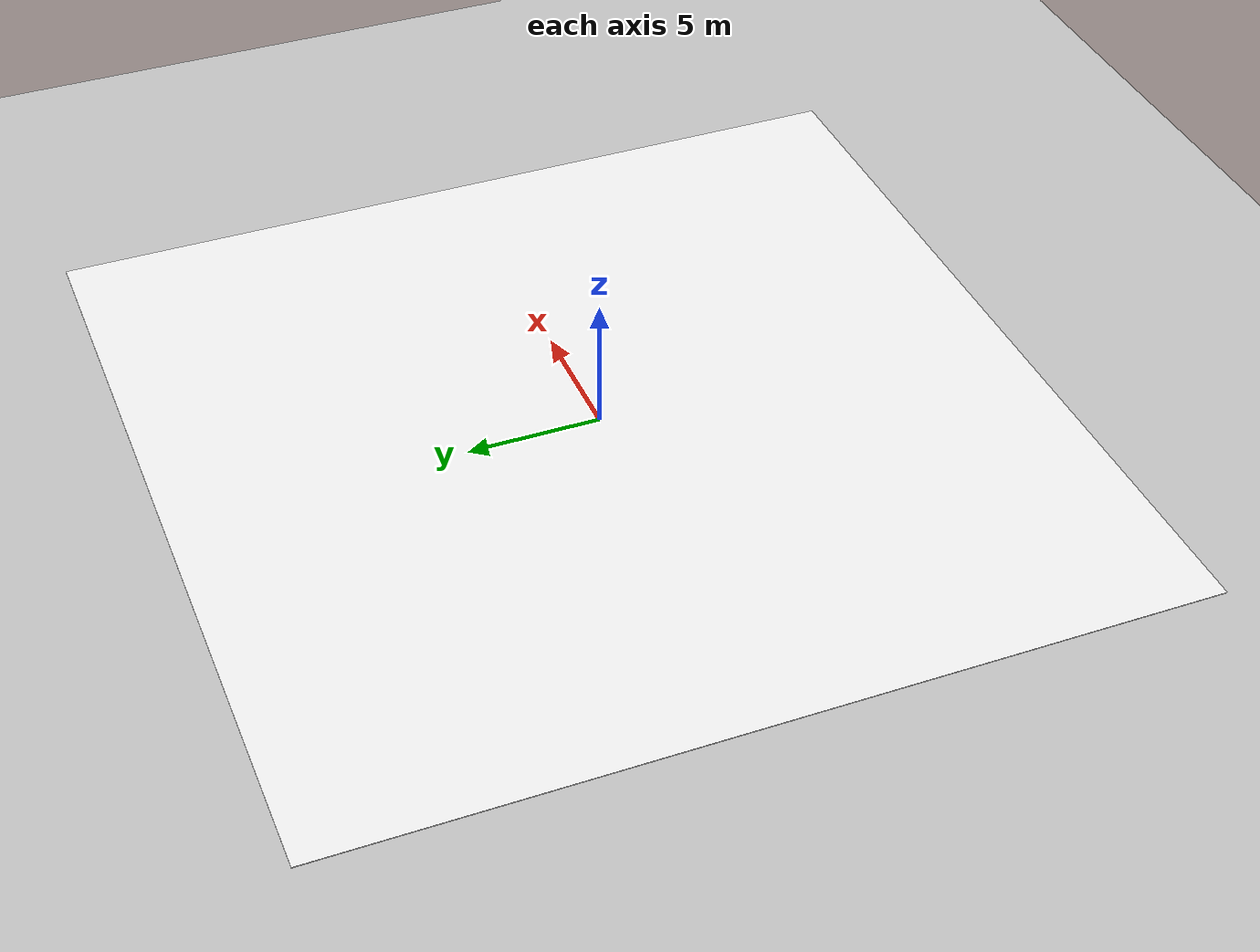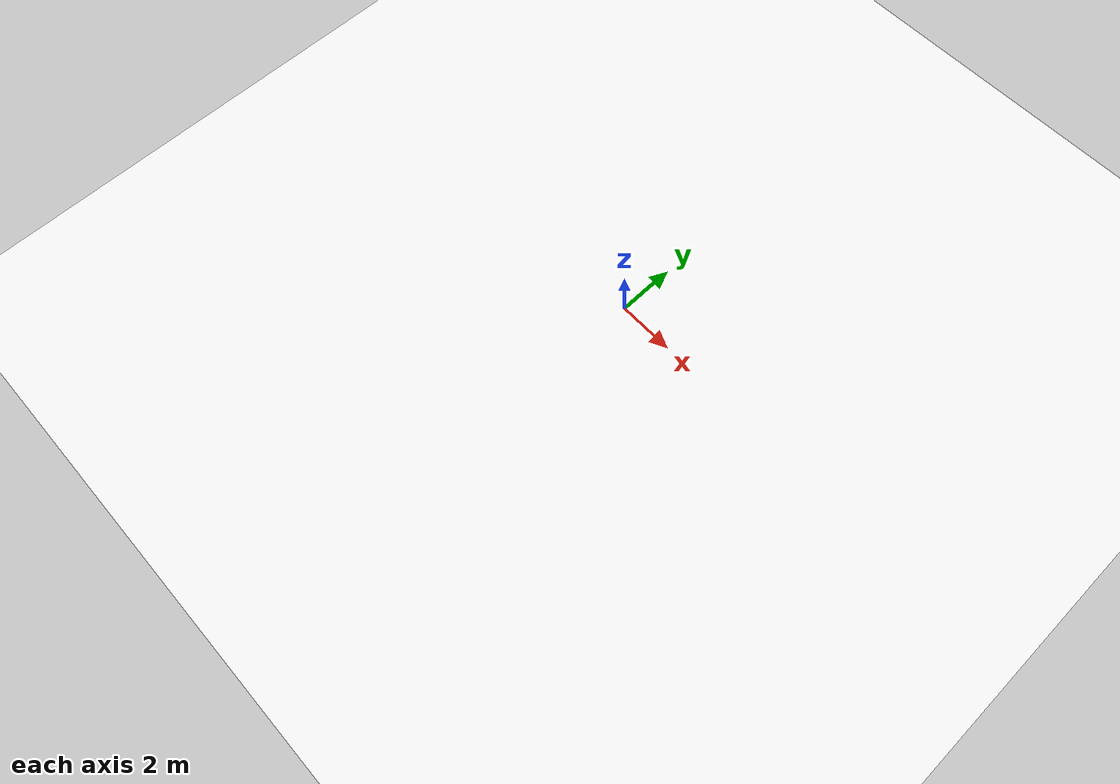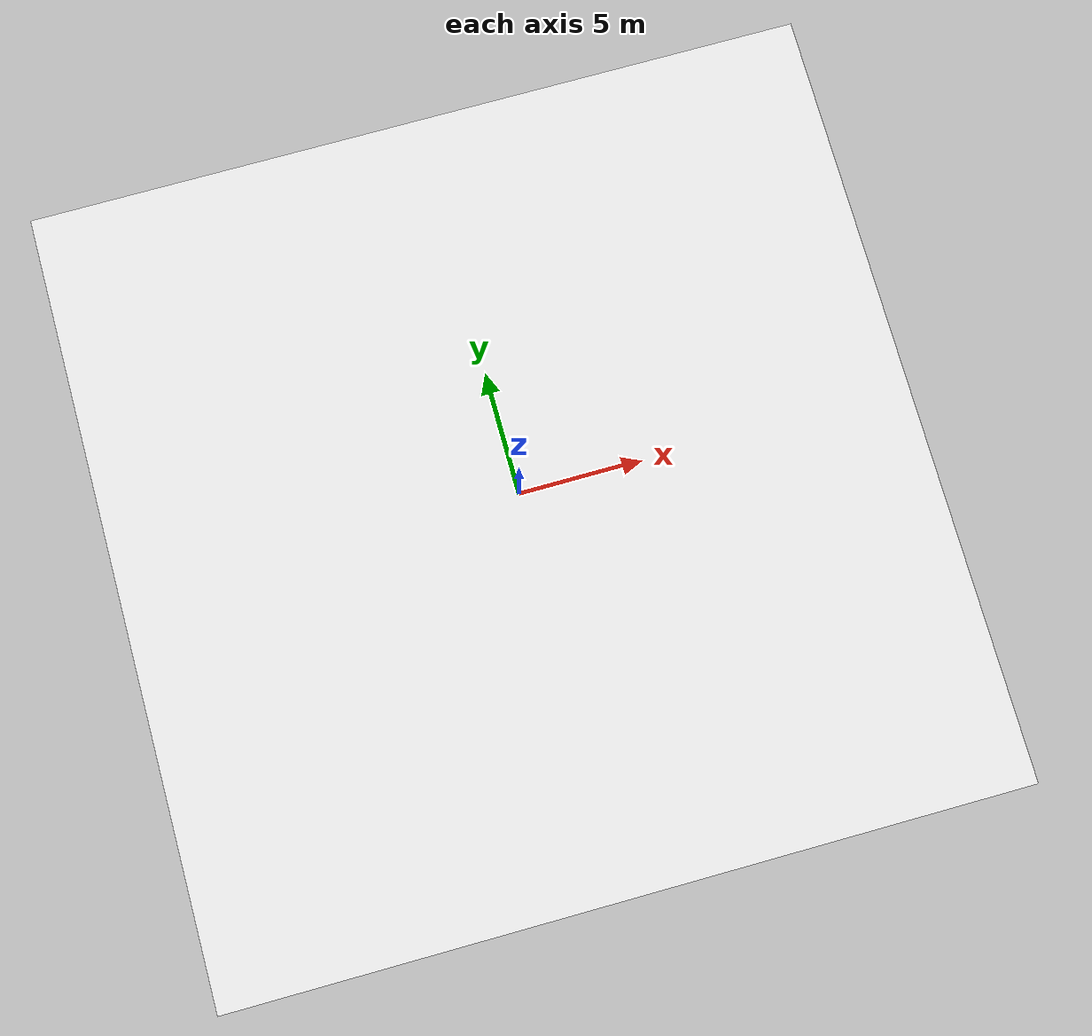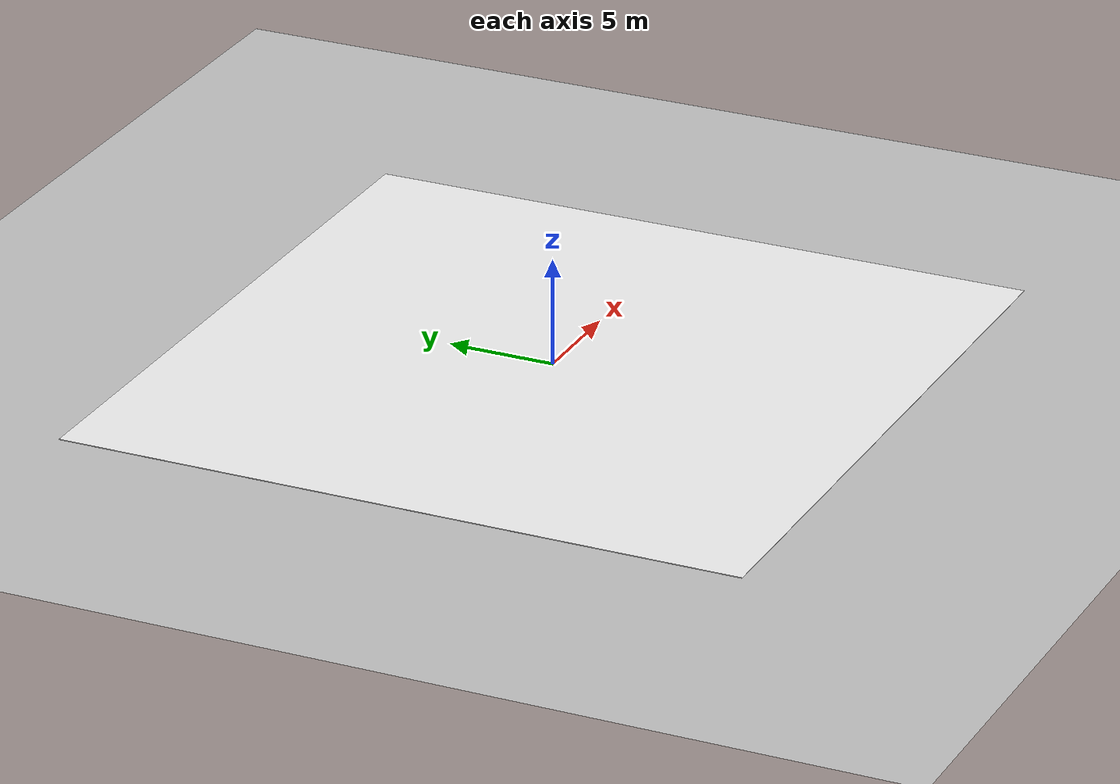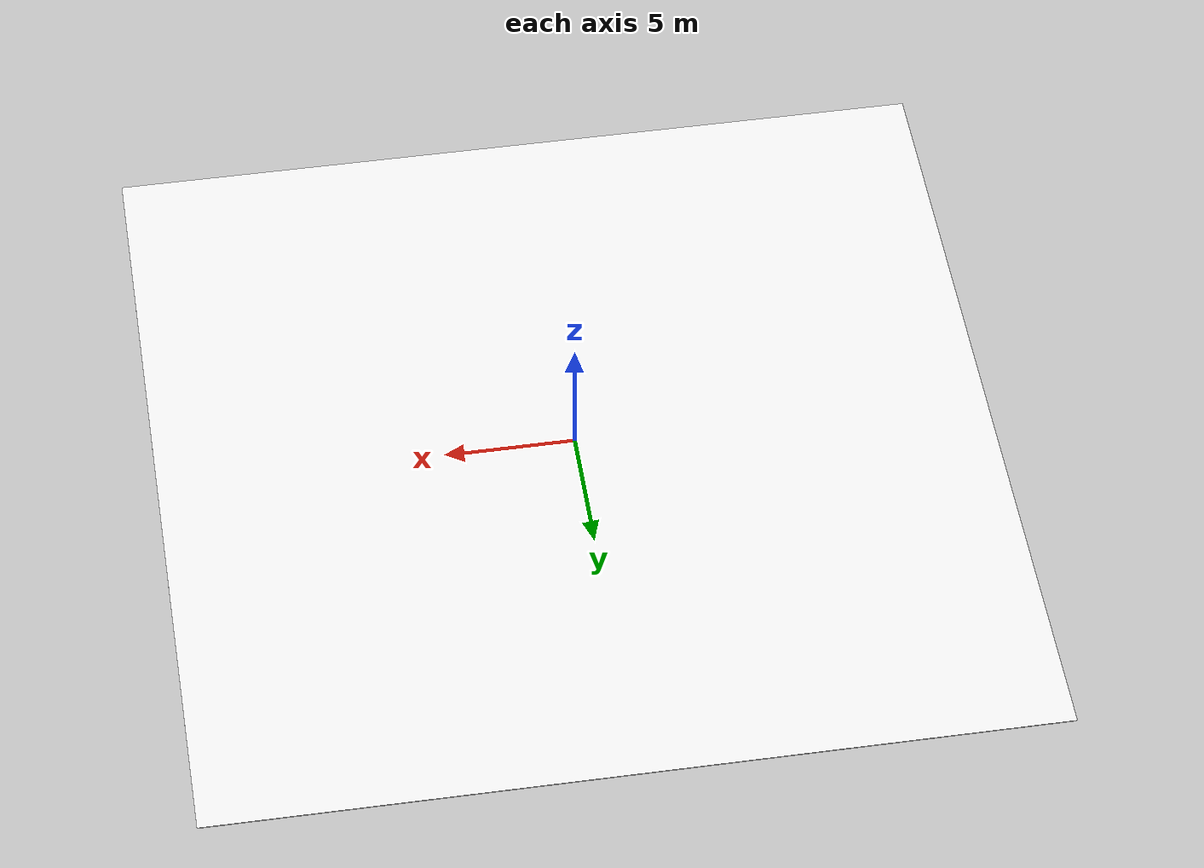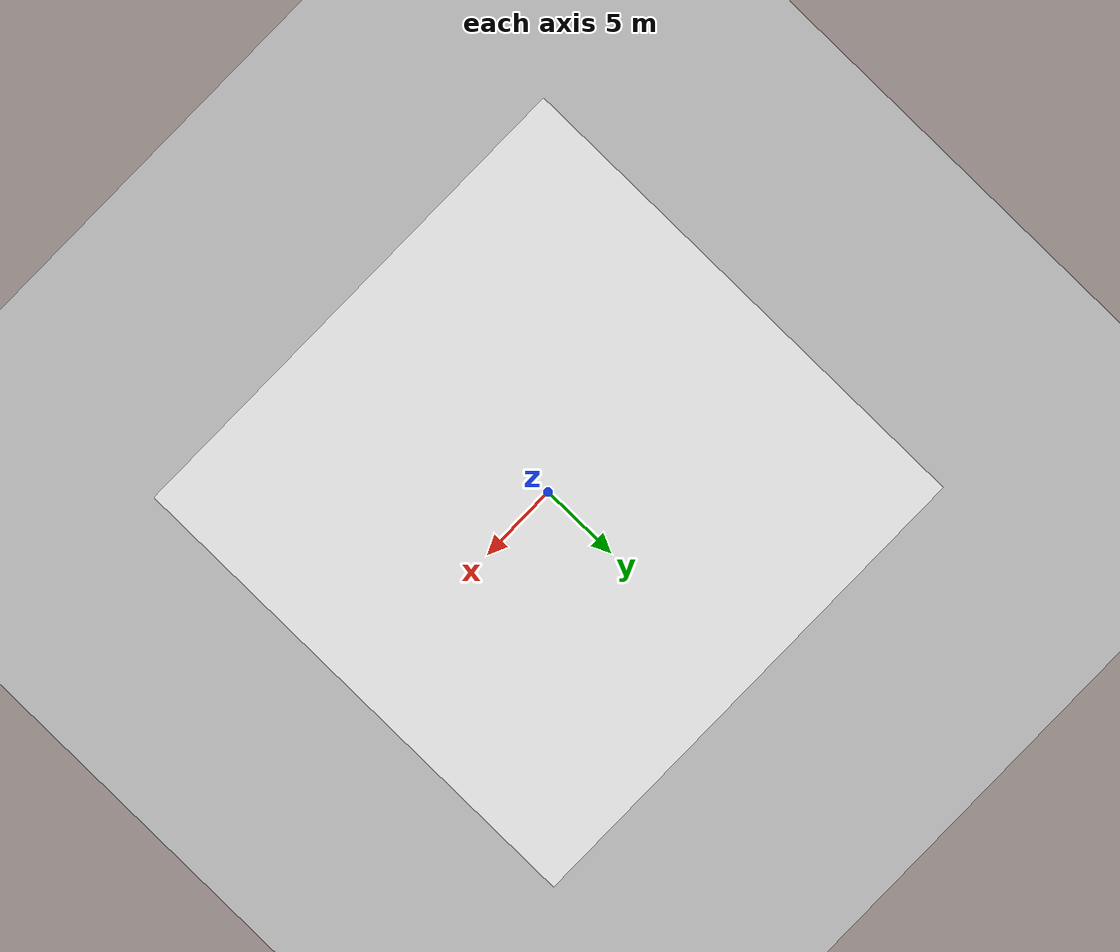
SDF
<?xml version="1.0" encoding="UTF-8"?>
<sdf version="1.9">
  <world name="v6_optical_flow">
    <physics type="ode"><max_step_size>0.004</max_step_size><real_time_factor>1.0</real_time_factor><real_time_update_rate>250</real_time_update_rate></physics>
    <gravity>0 0 -9.8</gravity>
    <magnetic_field>6e-06 2.3e-05 -4.2e-05</magnetic_field>
    <atmosphere type="adiabatic"/>
    <scene><grid>false</grid><ambient>0.4 0.4 0.4 1</ambient><background>0.7 0.7 0.7 1</background><shadows>true</shadows></scene>
    <model name="ground_plane"><static>true</static><link name="link">
      <collision name="collision"><geometry><plane><normal>0 0 1</normal><size>1 1</size></plane></geometry>
        <surface><friction><ode/></friction><bounce/><contact/></surface></collision>
      <visual name="visual"><geometry><plane><normal>0 0 1</normal><size>500 500</size></plane></geometry><material><ambient>0.8 0.8 0.8 1</ambient><diffuse>0.8 0.8 0.8 1</diffuse><specular>0.1 0.1 0.1 1</specular></material></visual>
      <pose>0 0 0 0 0 0</pose>
    </link></model>
    <model name="optical_flow_floor"><static>true</static>
      <link name="tile_-8_-8">
        <pose>-15 -15 0.006 0 0 0</pose>
        <visual name="visual">
          <geometry><box><size>2 2 0.01</size></box></geometry>
          <material><ambient>0.12 0.12 0.12 1</ambient><diffuse>0.12 0.12 0.12 1</diffuse><specular>0 0 0 1</specular></material>
        </visual>
      </link>
      <link name="tile_-8_-7">
        <pose>-15 -13 0.006 0 0 0</pose>
        <visual name="visual">
          <geometry><box><size>2 2 0.01</size></box></geometry>
          <material><ambient>0.65 0.65 0.65 1</ambient><diffuse>0.65 0.65 0.65 1</diffuse><specular>0 0 0 1</specular></material>
        </visual>
      </link>
      <link name="tile_-8_-6">
        <pose>-15 -11 0.006 0 0 0</pose>
        <visual name="visual">
          <geometry><box><size>2 2 0.01</size></box></geometry>
          <material><ambient>0.12 0.12 0.12 1</ambient><diffuse>0.12 0.12 0.12 1</diffuse><specular>0 0 0 1</specular></material>
        </visual>
      </link>
      <link name="tile_-8_-5">
        <pose>-15 -9 0.006 0 0 0</pose>
        <visual name="visual">
          <geometry><box><size>2 2 0.01</size></box></geometry>
          <material><ambient>0.65 0.65 0.65 1</ambient><diffuse>0.65 0.65 0.65 1</diffuse><specular>0 0 0 1</specular></material>
        </visual>
      </link>
      <link name="tile_-8_-4">
        <pose>-15 -7 0.006 0 0 0</pose>
        <visual name="visual">
          <geometry><box><size>2 2 0.01</size></box></geometry>
          <material><ambient>0.12 0.12 0.12 1</ambient><diffuse>0.12 0.12 0.12 1</diffuse><specular>0 0 0 1</specular></material>
        </visual>
      </link>
      <link name="tile_-8_-3">
        <pose>-15 -5 0.006 0 0 0</pose>
        <visual name="visual">
          <geometry><box><size>2 2 0.01</size></box></geometry>
          <material><ambient>0.65 0.65 0.65 1</ambient><diffuse>0.65 0.65 0.65 1</diffuse><specular>0 0 0 1</specular></material>
        </visual>
      </link>
      <link name="tile_-8_-2">
        <pose>-15 -3 0.006 0 0 0</pose>
        <visual name="visual">
          <geometry><box><size>2 2 0.01</size></box></geometry>
          <material><ambient>0.12 0.12 0.12 1</ambient><diffuse>0.12 0.12 0.12 1</diffuse><specular>0 0 0 1</specular></material>
        </visual>
      </link>
      <link name="tile_-8_-1">
        <pose>-15 -1 0.006 0 0 0</pose>
        <visual name="visual">
          <geometry><box><size>2 2 0.01</size></box></geometry>
          <material><ambient>0.65 0.65 0.65 1</ambient><diffuse>0.65 0.65 0.65 1</diffuse><specular>0 0 0 1</specular></material>
        </visual>
      </link>
      <link name="tile_-8_0">
        <pose>-15 1 0.006 0 0 0</pose>
        <visual name="visual">
          <geometry><box><size>2 2 0.01</size></box></geometry>
          <material><ambient>0.12 0.12 0.12 1</ambient><diffuse>0.12 0.12 0.12 1</diffuse><specular>0 0 0 1</specular></material>
        </visual>
      </link>
      <link name="tile_-8_1">
        <pose>-15 3 0.006 0 0 0</pose>
        <visual name="visual">
          <geometry><box><size>2 2 0.01</size></box></geometry>
          <material><ambient>0.65 0.65 0.65 1</ambient><diffuse>0.65 0.65 0.65 1</diffuse><specular>0 0 0 1</specular></material>
        </visual>
      </link>
      <link name="tile_-8_2">
        <pose>-15 5 0.006 0 0 0</pose>
        <visual name="visual">
          <geometry><box><size>2 2 0.01</size></box></geometry>
          <material><ambient>0.12 0.12 0.12 1</ambient><diffuse>0.12 0.12 0.12 1</diffuse><specular>0 0 0 1</specular></material>
        </visual>
      </link>
      <link name="tile_-8_3">
        <pose>-15 7 0.006 0 0 0</pose>
        <visual name="visual">
          <geometry><box><size>2 2 0.01</size></box></geometry>
          <material><ambient>0.65 0.65 0.65 1</ambient><diffuse>0.65 0.65 0.65 1</diffuse><specular>0 0 0 1</specular></material>
        </visual>
      </link>
      <link name="tile_-8_4">
        <pose>-15 9 0.006 0 0 0</pose>
        <visual name="visual">
          <geometry><box><size>2 2 0.01</size></box></geometry>
          <material><ambient>0.12 0.12 0.12 1</ambient><diffuse>0.12 0.12 0.12 1</diffuse><specular>0 0 0 1</specular></material>
        </visual>
      </link>
      <link name="tile_-8_5">
        <pose>-15 11 0.006 0 0 0</pose>
        <visual name="visual">
          <geometry><box><size>2 2 0.01</size></box></geometry>
          <material><ambient>0.65 0.65 0.65 1</ambient><diffuse>0.65 0.65 0.65 1</diffuse><specular>0 0 0 1</specular></material>
        </visual>
      </link>
      <link name="tile_-8_6">
        <pose>-15 13 0.006 0 0 0</pose>
        <visual name="visual">
          <geometry><box><size>2 2 0.01</size></box></geometry>
          <material><ambient>0.12 0.12 0.12 1</ambient><diffuse>0.12 0.12 0.12 1</diffuse><specular>0 0 0 1</specular></material>
        </visual>
      </link>
      <link name="tile_-8_7">
        <pose>-15 15 0.006 0 0 0</pose>
        <visual name="visual">
          <geometry><box><size>2 2 0.01</size></box></geometry>
          <material><ambient>0.65 0.65 0.65 1</ambient><diffuse>0.65 0.65 0.65 1</diffuse><specular>0 0 0 1</specular></material>
        </visual>
      </link>
      <link name="tile_-7_-8">
        <pose>-13 -15 0.006 0 0 0</pose>
        <visual name="visual">
          <geometry><box><size>2 2 0.01</size></box></geometry>
          <material><ambient>0.65 0.65 0.65 1</ambient><diffuse>0.65 0.65 0.65 1</diffuse><specular>0 0 0 1</specular></material>
        </visual>
      </link>
      <link name="tile_-7_-7">
        <pose>-13 -13 0.006 0 0 0</pose>
        <visual name="visual">
          <geometry><box><size>2 2 0.01</size></box></geometry>
          <material><ambient>0.12 0.12 0.12 1</ambient><diffuse>0.12 0.12 0.12 1</diffuse><specular>0 0 0 1</specular></material>
        </visual>
      </link>
      <link name="tile_-7_-6">
        <pose>-13 -11 0.006 0 0 0</pose>
        <visual name="visual">
          <geometry><box><size>2 2 0.01</size></box></geometry>
          <material><ambient>0.65 0.65 0.65 1</ambient><diffuse>0.65 0.65 0.65 1</diffuse><specular>0 0 0 1</specular></material>
        </visual>
      </link>
      <link name="tile_-7_-5">
        <pose>-13 -9 0.006 0 0 0</pose>
        <visual name="visual">
          <geometry><box><size>2 2 0.01</size></box></geometry>
          <material><ambient>0.12 0.12 0.12 1</ambient><diffuse>0.12 0.12 0.12 1</diffuse><specular>0 0 0 1</specular></material>
        </visual>
      </link>
      <link name="tile_-7_-4">
        <pose>-13 -7 0.006 0 0 0</pose>
        <visual name="visual">
          <geometry><box><size>2 2 0.01</size></box></geometry>
          <material><ambient>0.65 0.65 0.65 1</ambient><diffuse>0.65 0.65 0.65 1</diffuse><specular>0 0 0 1</specular></material>
        </visual>
      </link>
      <link name="tile_-7_-3">
        <pose>-13 -5 0.006 0 0 0</pose>
        <visual name="visual">
          <geometry><box><size>2 2 0.01</size></box></geometry>
          <material><ambient>0.12 0.12 0.12 1</ambient><diffuse>0.12 0.12 0.12 1</diffuse><specular>0 0 0 1</specular></material>
        </visual>
      </link>
      <link name="tile_-7_-2">
        <pose>-13 -3 0.006 0 0 0</pose>
        <visual name="visual">
          <geometry><box><size>2 2 0.01</size></box></geometry>
          <material><ambient>0.65 0.65 0.65 1</ambient><diffuse>0.65 0.65 0.65 1</diffuse><specular>0 0 0 1</specular></material>
        </visual>
      </link>
      <link name="tile_-7_-1">
        <pose>-13 -1 0.006 0 0 0</pose>
        <visual name="visual">
          <geometry><box><size>2 2 0.01</size></box></geometry>
          <material><ambient>0.12 0.12 0.12 1</ambient><diffuse>0.12 0.12 0.12 1</diffuse><specular>0 0 0 1</specular></material>
        </visual>
      </link>
      <link name="tile_-7_0">
        <pose>-13 1 0.006 0 0 0</pose>
        <visual name="visual">
          <geometry><box><size>2 2 0.01</size></box></geometry>
          <material><ambient>0.65 0.65 0.65 1</ambient><diffuse>0.65 0.65 0.65 1</diffuse><specular>0 0 0 1</specular></material>
        </visual>
      </link>
      <link name="tile_-7_1">
        <pose>-13 3 0.006 0 0 0</pose>
        <visual name="visual">
          <geometry><box><size>2 2 0.01</size></box></geometry>
          <material><ambient>0.12 0.12 0.12 1</ambient><diffuse>0.12 0.12 0.12 1</diffuse><specular>0 0 0 1</specular></material>
        </visual>
      </link>
      <link name="tile_-7_2">
        <pose>-13 5 0.006 0 0 0</pose>
        <visual name="visual">
          <geometry><box><size>2 2 0.01</size></box></geometry>
          <material><ambient>0.65 0.65 0.65 1</ambient><diffuse>0.65 0.65 0.65 1</diffuse><specular>0 0 0 1</specular></material>
        </visual>
      </link>
      <link name="tile_-7_3">
        <pose>-13 7 0.006 0 0 0</pose>
        <visual name="visual">
          <geometry><box><size>2 2 0.01</size></box></geometry>
          <material><ambient>0.12 0.12 0.12 1</ambient><diffuse>0.12 0.12 0.12 1</diffuse><specular>0 0 0 1</specular></material>
        </visual>
      </link>
      <link name="tile_-7_4">
        <pose>-13 9 0.006 0 0 0</pose>
        <visual name="visual">
          <geometry><box><size>2 2 0.01</size></box></geometry>
          <material><ambient>0.65 0.65 0.65 1</ambient><diffuse>0.65 0.65 0.65 1</diffuse><specular>0 0 0 1</specular></material>
        </visual>
      </link>
      <link name="tile_-7_5">
        <pose>-13 11 0.006 0 0 0</pose>
        <visual name="visual">
          <geometry><box><size>2 2 0.01</size></box></geometry>
          <material><ambient>0.12 0.12 0.12 1</ambient><diffuse>0.12 0.12 0.12 1</diffuse><specular>0 0 0 1</specular></material>
        </visual>
      </link>
      <link name="tile_-7_6">
        <pose>-13 13 0.006 0 0 0</pose>
        <visual name="visual">
          <geometry><box><size>2 2 0.01</size></box></geometry>
          <material><ambient>0.65 0.65 0.65 1</ambient><diffuse>0.65 0.65 0.65 1</diffuse><specular>0 0 0 1</specular></material>
        </visual>
      </link>
      <link name="tile_-7_7">
        <pose>-13 15 0.006 0 0 0</pose>
        <visual name="visual">
          <geometry><box><size>2 2 0.01</size></box></geometry>
          <material><ambient>0.12 0.12 0.12 1</ambient><diffuse>0.12 0.12 0.12 1</diffuse><specular>0 0 0 1</specular></material>
        </visual>
      </link>
      <link name="tile_-6_-8">
        <pose>-11 -15 0.006 0 0 0</pose>
        <visual name="visual">
          <geometry><box><size>2 2 0.01</size></box></geometry>
          <material><ambient>0.12 0.12 0.12 1</ambient><diffuse>0.12 0.12 0.12 1</diffuse><specular>0 0 0 1</specular></material>
        </visual>
      </link>
      <link name="tile_-6_-7">
        <pose>-11 -13 0.006 0 0 0</pose>
        <visual name="visual">
          <geometry><box><size>2 2 0.01</size></box></geometry>
          <material><ambient>0.65 0.65 0.65 1</ambient><diffuse>0.65 0.65 0.65 1</diffuse><specular>0 0 0 1</specular></material>
        </visual>
      </link>
      <link name="tile_-6_-6">
        <pose>-11 -11 0.006 0 0 0</pose>
        <visual name="visual">
          <geometry><box><size>2 2 0.01</size></box></geometry>
          <material><ambient>0.12 0.12 0.12 1</ambient><diffuse>0.12 0.12 0.12 1</diffuse><specular>0 0 0 1</specular></material>
        </visual>
      </link>
      <link name="tile_-6_-5">
        <pose>-11 -9 0.006 0 0 0</pose>
        <visual name="visual">
          <geometry><box><size>2 2 0.01</size></box></geometry>
          <material><ambient>0.65 0.65 0.65 1</ambient><diffuse>0.65 0.65 0.65 1</diffuse><specular>0 0 0 1</specular></material>
        </visual>
      </link>
      <link name="tile_-6_-4">
        <pose>-11 -7 0.006 0 0 0</pose>
        <visual name="visual">
          <geometry><box><size>2 2 0.01</size></box></geometry>
          <material><ambient>0.12 0.12 0.12 1</ambient><diffuse>0.12 0.12 0.12 1</diffuse><specular>0 0 0 1</specular></material>
        </visual>
      </link>
      <link name="tile_-6_-3">
        <pose>-11 -5 0.006 0 0 0</pose>
        <visual name="visual">
          <geometry><box><size>2 2 0.01</size></box></geometry>
          <material><ambient>0.65 0.65 0.65 1</ambient><diffuse>0.65 0.65 0.65 1</diffuse><specular>0 0 0 1</specular></material>
        </visual>
      </link>
      <link name="tile_-6_-2">
        <pose>-11 -3 0.006 0 0 0</pose>
        <visual name="visual">
          <geometry><box><size>2 2 0.01</size></box></geometry>
          <material><ambient>0.12 0.12 0.12 1</ambient><diffuse>0.12 0.12 0.12 1</diffuse><specular>0 0 0 1</specular></material>
        </visual>
      </link>
      <link name="tile_-6_-1">
        <pose>-11 -1 0.006 0 0 0</pose>
        <visual name="visual">
          <geometry><box><size>2 2 0.01</size></box></geometry>
          <material><ambient>0.65 0.65 0.65 1</ambient><diffuse>0.65 0.65 0.65 1</diffuse><specular>0 0 0 1</specular></material>
        </visual>
      </link>
      <link name="tile_-6_0">
        <pose>-11 1 0.006 0 0 0</pose>
        <visual name="visual">
          <geometry><box><size>2 2 0.01</size></box></geometry>
          <material><ambient>0.12 0.12 0.12 1</ambient><diffuse>0.12 0.12 0.12 1</diffuse><specular>0 0 0 1</specular></material>
        </visual>
      </link>
      <link name="tile_-6_1">
        <pose>-11 3 0.006 0 0 0</pose>
        <visual name="visual">
          <geometry><box><size>2 2 0.01</size></box></geometry>
          <material><ambient>0.65 0.65 0.65 1</ambient><diffuse>0.65 0.65 0.65 1</diffuse><specular>0 0 0 1</specular></material>
        </visual>
      </link>
      <link name="tile_-6_2">
        <pose>-11 5 0.006 0 0 0</pose>
        <visual name="visual">
          <geometry><box><size>2 2 0.01</size></box></geometry>
          <material><ambient>0.12 0.12 0.12 1</ambient><diffuse>0.12 0.12 0.12 1</diffuse><specular>0 0 0 1</specular></material>
        </visual>
      </link>
      <link name="tile_-6_3">
        <pose>-11 7 0.006 0 0 0</pose>
        <visual name="visual">
          <geometry><box><size>2 2 0.01</size></box></geometry>
          <material><ambient>0.65 0.65 0.65 1</ambient><diffuse>0.65 0.65 0.65 1</diffuse><specular>0 0 0 1</specular></material>
        </visual>
      </link>
      <link name="tile_-6_4">
        <pose>-11 9 0.006 0 0 0</pose>
        <visual name="visual">
          <geometry><box><size>2 2 0.01</size></box></geometry>
          <material><ambient>0.12 0.12 0.12 1</ambient><diffuse>0.12 0.12 0.12 1</diffuse><specular>0 0 0 1</specular></material>
        </visual>
      </link>
      <link name="tile_-6_5">
        <pose>-11 11 0.006 0 0 0</pose>
        <visual name="visual">
          <geometry><box><size>2 2 0.01</size></box></geometry>
          <material><ambient>0.65 0.65 0.65 1</ambient><diffuse>0.65 0.65 0.65 1</diffuse><specular>0 0 0 1</specular></material>
        </visual>
      </link>
      <link name="tile_-6_6">
        <pose>-11 13 0.006 0 0 0</pose>
        <visual name="visual">
          <geometry><box><size>2 2 0.01</size></box></geometry>
          <material><ambient>0.12 0.12 0.12 1</ambient><diffuse>0.12 0.12 0.12 1</diffuse><specular>0 0 0 1</specular></material>
        </visual>
      </link>
      <link name="tile_-6_7">
        <pose>-11 15 0.006 0 0 0</pose>
        <visual name="visual">
          <geometry><box><size>2 2 0.01</size></box></geometry>
          <material><ambient>0.65 0.65 0.65 1</ambient><diffuse>0.65 0.65 0.65 1</diffuse><specular>0 0 0 1</specular></material>
        </visual>
      </link>
      <link name="tile_-5_-8">
        <pose>-9 -15 0.006 0 0 0</pose>
        <visual name="visual">
          <geometry><box><size>2 2 0.01</size></box></geometry>
          <material><ambient>0.65 0.65 0.65 1</ambient><diffuse>0.65 0.65 0.65 1</diffuse><specular>0 0 0 1</specular></material>
        </visual>
      </link>
      <link name="tile_-5_-7">
        <pose>-9 -13 0.006 0 0 0</pose>
        <visual name="visual">
          <geometry><box><size>2 2 0.01</size></box></geometry>
          <material><ambient>0.12 0.12 0.12 1</ambient><diffuse>0.12 0.12 0.12 1</diffuse><specular>0 0 0 1</specular></material>
        </visual>
      </link>
      <link name="tile_-5_-6">
        <pose>-9 -11 0.006 0 0 0</pose>
        <visual name="visual">
          <geometry><box><size>2 2 0.01</size></box></geometry>
          <material><ambient>0.65 0.65 0.65 1</ambient><diffuse>0.65 0.65 0.65 1</diffuse><specular>0 0 0 1</specular></material>
        </visual>
      </link>
      <link name="tile_-5_-5">
        <pose>-9 -9 0.006 0 0 0</pose>
        <visual name="visual">
          <geometry><box><size>2 2 0.01</size></box></geometry>
          <material><ambient>0.12 0.12 0.12 1</ambient><diffuse>0.12 0.12 0.12 1</diffuse><specular>0 0 0 1</specular></material>
        </visual>
      </link>
      <link name="tile_-5_-4">
        <pose>-9 -7 0.006 0 0 0</pose>
        <visual name="visual">
          <geometry><box><size>2 2 0.01</size></box></geometry>
          <material><ambient>0.65 0.65 0.65 1</ambient><diffuse>0.65 0.65 0.65 1</diffuse><specular>0 0 0 1</specular></material>
        </visual>
      </link>
      <link name="tile_-5_-3">
        <pose>-9 -5 0.006 0 0 0</pose>
        <visual name="visual">
          <geometry><box><size>2 2 0.01</size></box></geometry>
          <material><ambient>0.12 0.12 0.12 1</ambient><diffuse>0.12 0.12 0.12 1</diffuse><specular>0 0 0 1</specular></material>
        </visual>
      </link>
      <link name="tile_-5_-2">
        <pose>-9 -3 0.006 0 0 0</pose>
        <visual name="visual">
          <geometry><box><size>2 2 0.01</size></box></geometry>
          <material><ambient>0.65 0.65 0.65 1</ambient><diffuse>0.65 0.65 0.65 1</diffuse><specular>0 0 0 1</specular></material>
        </visual>
      </link>
      <link name="tile_-5_-1">
        <pose>-9 -1 0.006 0 0 0</pose>
        <visual name="visual">
          <geometry><box><size>2 2 0.01</size></box></geometry>
          <material><ambient>0.12 0.12 0.12 1</ambient><diffuse>0.12 0.12 0.12 1</diffuse><specular>0 0 0 1</specular></material>
        </visual>
      </link>
      <link name="tile_-5_0">
        <pose>-9 1 0.006 0 0 0</pose>
        <visual name="visual">
          <geometry><box><size>2 2 0.01</size></box></geometry>
          <material><ambient>0.65 0.65 0.65 1</ambient><diffuse>0.65 0.65 0.65 1</diffuse><specular>0 0 0 1</specular></material>
        </visual>
      </link>
      <link name="tile_-5_1">
        <pose>-9 3 0.006 0 0 0</pose>
        <visual name="visual">
          <geometry><box><size>2 2 0.01</size></box></geometry>
          <material><ambient>0.12 0.12 0.12 1</ambient><diffuse>0.12 0.12 0.12 1</diffuse><specular>0 0 0 1</specular></material>
        </visual>
      </link>
      <link name="tile_-5_2">
        <pose>-9 5 0.006 0 0 0</pose>
        <visual name="visual">
          <geometry><box><size>2 2 0.01</size></box></geometry>
          <material><ambient>0.65 0.65 0.65 1</ambient><diffuse>0.65 0.65 0.65 1</diffuse><specular>0 0 0 1</specular></material>
        </visual>
      </link>
      <link name="tile_-5_3">
        <pose>-9 7 0.006 0 0 0</pose>
        <visual name="visual">
          <geometry><box><size>2 2 0.01</size></box></geometry>
          <material><ambient>0.12 0.12 0.12 1</ambient><diffuse>0.12 0.12 0.12 1</diffuse><specular>0 0 0 1</specular></material>
        </visual>
      </link>
      <link name="tile_-5_4">
        <pose>-9 9 0.006 0 0 0</pose>
        <visual name="visual">
          <geometry><box><size>2 2 0.01</size></box></geometry>
          <material><ambient>0.65 0.65 0.65 1</ambient><diffuse>0.65 0.65 0.65 1</diffuse><specular>0 0 0 1</specular></material>
        </visual>
      </link>
      <link name="tile_-5_5">
        <pose>-9 11 0.006 0 0 0</pose>
        <visual name="visual">
          <geometry><box><size>2 2 0.01</size></box></geometry>
          <material><ambient>0.12 0.12 0.12 1</ambient><diffuse>0.12 0.12 0.12 1</diffuse><specular>0 0 0 1</specular></material>
        </visual>
      </link>
      <link name="tile_-5_6">
        <pose>-9 13 0.006 0 0 0</pose>
        <visual name="visual">
          <geometry><box><size>2 2 0.01</size></box></geometry>
          <material><ambient>0.65 0.65 0.65 1</ambient><diffuse>0.65 0.65 0.65 1</diffuse><specular>0 0 0 1</specular></material>
        </visual>
      </link>
      <link name="tile_-5_7">
        <pose>-9 15 0.006 0 0 0</pose>
        <visual name="visual">
          <geometry><box><size>2 2 0.01</size></box></geometry>
          <material><ambient>0.12 0.12 0.12 1</ambient><diffuse>0.12 0.12 0.12 1</diffuse><specular>0 0 0 1</specular></material>
        </visual>
      </link>
      <link name="tile_-4_-8">
        <pose>-7 -15 0.006 0 0 0</pose>
        <visual name="visual">
          <geometry><box><size>2 2 0.01</size></box></geometry>
          <material><ambient>0.12 0.12 0.12 1</ambient><diffuse>0.12 0.12 0.12 1</diffuse><specular>0 0 0 1</specular></material>
        </visual>
      </link>
      <link name="tile_-4_-7">
        <pose>-7 -13 0.006 0 0 0</pose>
        <visual name="visual">
          <geometry><box><size>2 2 0.01</size></box></geometry>
          <material><ambient>0.65 0.65 0.65 1</ambient><diffuse>0.65 0.65 0.65 1</diffuse><specular>0 0 0 1</specular></material>
        </visual>
      </link>
      <link name="tile_-4_-6">
        <pose>-7 -11 0.006 0 0 0</pose>
        <visual name="visual">
          <geometry><box><size>2 2 0.01</size></box></geometry>
          <material><ambient>0.12 0.12 0.12 1</ambient><diffuse>0.12 0.12 0.12 1</diffuse><specular>0 0 0 1</specular></material>
        </visual>
      </link>
      <link name="tile_-4_-5">
        <pose>-7 -9 0.006 0 0 0</pose>
        <visual name="visual">
          <geometry><box><size>2 2 0.01</size></box></geometry>
          <material><ambient>0.65 0.65 0.65 1</ambient><diffuse>0.65 0.65 0.65 1</diffuse><specular>0 0 0 1</specular></material>
        </visual>
      </link>
      <link name="tile_-4_-4">
        <pose>-7 -7 0.006 0 0 0</pose>
        <visual name="visual">
          <geometry><box><size>2 2 0.01</size></box></geometry>
          <material><ambient>0.12 0.12 0.12 1</ambient><diffuse>0.12 0.12 0.12 1</diffuse><specular>0 0 0 1</specular></material>
        </visual>
      </link>
      <link name="tile_-4_-3">
        <pose>-7 -5 0.006 0 0 0</pose>
        <visual name="visual">
          <geometry><box><size>2 2 0.01</size></box></geometry>
          <material><ambient>0.65 0.65 0.65 1</ambient><diffuse>0.65 0.65 0.65 1</diffuse><specular>0 0 0 1</specular></material>
        </visual>
      </link>
      <link name="tile_-4_-2">
        <pose>-7 -3 0.006 0 0 0</pose>
        <visual name="visual">
          <geometry><box><size>2 2 0.01</size></box></geometry>
          <material><ambient>0.12 0.12 0.12 1</ambient><diffuse>0.12 0.12 0.12 1</diffuse><specular>0 0 0 1</specular></material>
        </visual>
      </link>
      <link name="tile_-4_-1">
        <pose>-7 -1 0.006 0 0 0</pose>
        <visual name="visual">
          <geometry><box><size>2 2 0.01</size></box></geometry>
          <material><ambient>0.65 0.65 0.65 1</ambient><diffuse>0.65 0.65 0.65 1</diffuse><specular>0 0 0 1</specular></material>
        </visual>
      </link>
      <link name="tile_-4_0">
        <pose>-7 1 0.006 0 0 0</pose>
        <visual name="visual">
          <geometry><box><size>2 2 0.01</size></box></geometry>
          <material><ambient>0.12 0.12 0.12 1</ambient><diffuse>0.12 0.12 0.12 1</diffuse><specular>0 0 0 1</specular></material>
        </visual>
      </link>
      <link name="tile_-4_1">
        <pose>-7 3 0.006 0 0 0</pose>
        <visual name="visual">
          <geometry><box><size>2 2 0.01</size></box></geometry>
          <material><ambient>0.65 0.65 0.65 1</ambient><diffuse>0.65 0.65 0.65 1</diffuse><specular>0 0 0 1</specular></material>
        </visual>
      </link>
      <link name="tile_-4_2">
        <pose>-7 5 0.006 0 0 0</pose>
        <visual name="visual">
          <geometry><box><size>2 2 0.01</size></box></geometry>
          <material><ambient>0.12 0.12 0.12 1</ambient><diffuse>0.12 0.12 0.12 1</diffuse><specular>0 0 0 1</specular></material>
        </visual>
      </link>
      <link name="tile_-4_3">
        <pose>-7 7 0.006 0 0 0</pose>
        <visual name="visual">
          <geometry><box><size>2 2 0.01</size></box></geometry>
          <material><ambient>0.65 0.65 0.65 1</ambient><diffuse>0.65 0.65 0.65 1</diffuse><specular>0 0 0 1</specular></material>
        </visual>
      </link>
      <link name="tile_-4_4">
        <pose>-7 9 0.006 0 0 0</pose>
        <visual name="visual">
          <geometry><box><size>2 2 0.01</size></box></geometry>
          <material><ambient>0.12 0.12 0.12 1</ambient><diffuse>0.12 0.12 0.12 1</diffuse><specular>0 0 0 1</specular></material>
        </visual>
      </link>
      <link name="tile_-4_5">
        <pose>-7 11 0.006 0 0 0</pose>
        <visual name="visual">
          <geometry><box><size>2 2 0.01</size></box></geometry>
          <material><ambient>0.65 0.65 0.65 1</ambient><diffuse>0.65 0.65 0.65 1</diffuse><specular>0 0 0 1</specular></material>
        </visual>
      </link>
      <link name="tile_-4_6">
        <pose>-7 13 0.006 0 0 0</pose>
        <visual name="visual">
          <geometry><box><size>2 2 0.01</size></box></geometry>
          <material><ambient>0.12 0.12 0.12 1</ambient><diffuse>0.12 0.12 0.12 1</diffuse><specular>0 0 0 1</specular></material>
        </visual>
      </link>
      <link name="tile_-4_7">
        <pose>-7 15 0.006 0 0 0</pose>
        <visual name="visual">
          <geometry><box><size>2 2 0.01</size></box></geometry>
          <material><ambient>0.65 0.65 0.65 1</ambient><diffuse>0.65 0.65 0.65 1</diffuse><specular>0 0 0 1</specular></material>
        </visual>
      </link>
      <link name="tile_-3_-8">
        <pose>-5 -15 0.006 0 0 0</pose>
        <visual name="visual">
          <geometry><box><size>2 2 0.01</size></box></geometry>
          <material><ambient>0.65 0.65 0.65 1</ambient><diffuse>0.65 0.65 0.65 1</diffuse><specular>0 0 0 1</specular></material>
        </visual>
      </link>
      <link name="tile_-3_-7">
        <pose>-5 -13 0.006 0 0 0</pose>
        <visual name="visual">
          <geometry><box><size>2 2 0.01</size></box></geometry>
          <material><ambient>0.12 0.12 0.12 1</ambient><diffuse>0.12 0.12 0.12 1</diffuse><specular>0 0 0 1</specular></material>
        </visual>
      </link>
      <link name="tile_-3_-6">
        <pose>-5 -11 0.006 0 0 0</pose>
        <visual name="visual">
          <geometry><box><size>2 2 0.01</size></box></geometry>
          <material><ambient>0.65 0.65 0.65 1</ambient><diffuse>0.65 0.65 0.65 1</diffuse><specular>0 0 0 1</specular></material>
        </visual>
      </link>
      <link name="tile_-3_-5">
        <pose>-5 -9 0.006 0 0 0</pose>
        <visual name="visual">
          <geometry><box><size>2 2 0.01</size></box></geometry>
          <material><ambient>0.12 0.12 0.12 1</ambient><diffuse>0.12 0.12 0.12 1</diffuse><specular>0 0 0 1</specular></material>
        </visual>
      </link>
      <link name="tile_-3_-4">
        <pose>-5 -7 0.006 0 0 0</pose>
        <visual name="visual">
          <geometry><box><size>2 2 0.01</size></box></geometry>
          <material><ambient>0.65 0.65 0.65 1</ambient><diffuse>0.65 0.65 0.65 1</diffuse><specular>0 0 0 1</specular></material>
        </visual>
      </link>
      <link name="tile_-3_-3">
        <pose>-5 -5 0.006 0 0 0</pose>
        <visual name="visual">
          <geometry><box><size>2 2 0.01</size></box></geometry>
          <material><ambient>0.12 0.12 0.12 1</ambient><diffuse>0.12 0.12 0.12 1</diffuse><specular>0 0 0 1</specular></material>
        </visual>
      </link>
      <link name="tile_-3_-2">
        <pose>-5 -3 0.006 0 0 0</pose>
        <visual name="visual">
          <geometry><box><size>2 2 0.01</size></box></geometry>
          <material><ambient>0.65 0.65 0.65 1</ambient><diffuse>0.65 0.65 0.65 1</diffuse><specular>0 0 0 1</specular></material>
        </visual>
      </link>
      <link name="tile_-3_-1">
        <pose>-5 -1 0.006 0 0 0</pose>
        <visual name="visual">
          <geometry><box><size>2 2 0.01</size></box></geometry>
          <material><ambient>0.12 0.12 0.12 1</ambient><diffuse>0.12 0.12 0.12 1</diffuse><specular>0 0 0 1</specular></material>
        </visual>
      </link>
      <link name="tile_-3_0">
        <pose>-5 1 0.006 0 0 0</pose>
        <visual name="visual">
          <geometry><box><size>2 2 0.01</size></box></geometry>
          <material><ambient>0.65 0.65 0.65 1</ambient><diffuse>0.65 0.65 0.65 1</diffuse><specular>0 0 0 1</specular></material>
        </visual>
      </link>
      <link name="tile_-3_1">
        <pose>-5 3 0.006 0 0 0</pose>
        <visual name="visual">
          <geometry><box><size>2 2 0.01</size></box></geometry>
          <material><ambient>0.12 0.12 0.12 1</ambient><diffuse>0.12 0.12 0.12 1</diffuse><specular>0 0 0 1</specular></material>
        </visual>
      </link>
      <link name="tile_-3_2">
        <pose>-5 5 0.006 0 0 0</pose>
        <visual name="visual">
          <geometry><box><size>2 2 0.01</size></box></geometry>
          <material><ambient>0.65 0.65 0.65 1</ambient><diffuse>0.65 0.65 0.65 1</diffuse><specular>0 0 0 1</specular></material>
        </visual>
      </link>
      <link name="tile_-3_3">
        <pose>-5 7 0.006 0 0 0</pose>
        <visual name="visual">
          <geometry><box><size>2 2 0.01</size></box></geometry>
          <material><ambient>0.12 0.12 0.12 1</ambient><diffuse>0.12 0.12 0.12 1</diffuse><specular>0 0 0 1</specular></material>
        </visual>
      </link>
      <link name="tile_-3_4">
        <pose>-5 9 0.006 0 0 0</pose>
        <visual name="visual">
          <geometry><box><size>2 2 0.01</size></box></geometry>
          <material><ambient>0.65 0.65 0.65 1</ambient><diffuse>0.65 0.65 0.65 1</diffuse><specular>0 0 0 1</specular></material>
        </visual>
      </link>
      <link name="tile_-3_5">
        <pose>-5 11 0.006 0 0 0</pose>
        <visual name="visual">
          <geometry><box><size>2 2 0.01</size></box></geometry>
          <material><ambient>0.12 0.12 0.12 1</ambient><diffuse>0.12 0.12 0.12 1</diffuse><specular>0 0 0 1</specular></material>
        </visual>
      </link>
      <link name="tile_-3_6">
        <pose>-5 13 0.006 0 0 0</pose>
        <visual name="visual">
          <geometry><box><size>2 2 0.01</size></box></geometry>
          <material><ambient>0.65 0.65 0.65 1</ambient><diffuse>0.65 0.65 0.65 1</diffuse><specular>0 0 0 1</specular></material>
        </visual>
      </link>
      <link name="tile_-3_7">
        <pose>-5 15 0.006 0 0 0</pose>
        <visual name="visual">
          <geometry><box><size>2 2 0.01</size></box></geometry>
          <material><ambient>0.12 0.12 0.12 1</ambient><diffuse>0.12 0.12 0.12 1</diffuse><specular>0 0 0 1</specular></material>
        </visual>
      </link>
      <link name="tile_-2_-8">
        <pose>-3 -15 0.006 0 0 0</pose>
        <visual name="visual">
          <geometry><box><size>2 2 0.01</size></box></geometry>
          <material><ambient>0.12 0.12 0.12 1</ambient><diffuse>0.12 0.12 0.12 1</diffuse><specular>0 0 0 1</specular></material>
        </visual>
      </link>
      <link name="tile_-2_-7">
        <pose>-3 -13 0.006 0 0 0</pose>
        <visual name="visual">
          <geometry><box><size>2 2 0.01</size></box></geometry>
          <material><ambient>0.65 0.65 0.65 1</ambient><diffuse>0.65 0.65 0.65 1</diffuse><specular>0 0 0 1</specular></material>
        </visual>
      </link>
      <link name="tile_-2_-6">
        <pose>-3 -11 0.006 0 0 0</pose>
        <visual name="visual">
          <geometry><box><size>2 2 0.01</size></box></geometry>
          <material><ambient>0.12 0.12 0.12 1</ambient><diffuse>0.12 0.12 0.12 1</diffuse><specular>0 0 0 1</specular></material>
        </visual>
      </link>
      <link name="tile_-2_-5">
        <pose>-3 -9 0.006 0 0 0</pose>
        <visual name="visual">
          <geometry><box><size>2 2 0.01</size></box></geometry>
          <material><ambient>0.65 0.65 0.65 1</ambient><diffuse>0.65 0.65 0.65 1</diffuse><specular>0 0 0 1</specular></material>
        </visual>
      </link>
      <link name="tile_-2_-4">
        <pose>-3 -7 0.006 0 0 0</pose>
        <visual name="visual">
          <geometry><box><size>2 2 0.01</size></box></geometry>
          <material><ambient>0.12 0.12 0.12 1</ambient><diffuse>0.12 0.12 0.12 1</diffuse><specular>0 0 0 1</specular></material>
        </visual>
      </link>
      <link name="tile_-2_-3">
        <pose>-3 -5 0.006 0 0 0</pose>
        <visual name="visual">
          <geometry><box><size>2 2 0.01</size></box></geometry>
          <material><ambient>0.65 0.65 0.65 1</ambient><diffuse>0.65 0.65 0.65 1</diffuse><specular>0 0 0 1</specular></material>
        </visual>
      </link>
      <link name="tile_-2_-2">
        <pose>-3 -3 0.006 0 0 0</pose>
        <visual name="visual">
          <geometry><box><size>2 2 0.01</size></box></geometry>
          <material><ambient>0.12 0.12 0.12 1</ambient><diffuse>0.12 0.12 0.12 1</diffuse><specular>0 0 0 1</specular></material>
        </visual>
      </link>
      <link name="tile_-2_-1">
        <pose>-3 -1 0.006 0 0 0</pose>
        <visual name="visual">
          <geometry><box><size>2 2 0.01</size></box></geometry>
          <material><ambient>0.65 0.65 0.65 1</ambient><diffuse>0.65 0.65 0.65 1</diffuse><specular>0 0 0 1</specular></material>
        </visual>
      </link>
      <link name="tile_-2_0">
        <pose>-3 1 0.006 0 0 0</pose>
        <visual name="visual">
          <geometry><box><size>2 2 0.01</size></box></geometry>
          <material><ambient>0.12 0.12 0.12 1</ambient><diffuse>0.12 0.12 0.12 1</diffuse><specular>0 0 0 1</specular></material>
        </visual>
      </link>
      <link name="tile_-2_1">
        <pose>-3 3 0.006 0 0 0</pose>
        <visual name="visual">
          <geometry><box><size>2 2 0.01</size></box></geometry>
          <material><ambient>0.65 0.65 0.65 1</ambient><diffuse>0.65 0.65 0.65 1</diffuse><specular>0 0 0 1</specular></material>
        </visual>
      </link>
      <link name="tile_-2_2">
        <pose>-3 5 0.006 0 0 0</pose>
        <visual name="visual">
          <geometry><box><size>2 2 0.01</size></box></geometry>
          <material><ambient>0.12 0.12 0.12 1</ambient><diffuse>0.12 0.12 0.12 1</diffuse><specular>0 0 0 1</specular></material>
        </visual>
      </link>
      <link name="tile_-2_3">
        <pose>-3 7 0.006 0 0 0</pose>
        <visual name="visual">
          <geometry><box><size>2 2 0.01</size></box></geometry>
          <material><ambient>0.65 0.65 0.65 1</ambient><diffuse>0.65 0.65 0.65 1</diffuse><specular>0 0 0 1</specular></material>
        </visual>
      </link>
      <link name="tile_-2_4">
        <pose>-3 9 0.006 0 0 0</pose>
        <visual name="visual">
          <geometry><box><size>2 2 0.01</size></box></geometry>
          <material><ambient>0.12 0.12 0.12 1</ambient><diffuse>0.12 0.12 0.12 1</diffuse><specular>0 0 0 1</specular></material>
        </visual>
      </link>
      <link name="tile_-2_5">
        <pose>-3 11 0.006 0 0 0</pose>
        <visual name="visual">
          <geometry><box><size>2 2 0.01</size></box></geometry>
          <material><ambient>0.65 0.65 0.65 1</ambient><diffuse>0.65 0.65 0.65 1</diffuse><specular>0 0 0 1</specular></material>
        </visual>
      </link>
      <link name="tile_-2_6">
        <pose>-3 13 0.006 0 0 0</pose>
        <visual name="visual">
          <geometry><box><size>2 2 0.01</size></box></geometry>
          <material><ambient>0.12 0.12 0.12 1</ambient><diffuse>0.12 0.12 0.12 1</diffuse><specular>0 0 0 1</specular></material>
        </visual>
      </link>
      <link name="tile_-2_7">
        <pose>-3 15 0.006 0 0 0</pose>
        <visual name="visual">
          <geometry><box><size>2 2 0.01</size></box></geometry>
          <material><ambient>0.65 0.65 0.65 1</ambient><diffuse>0.65 0.65 0.65 1</diffuse><specular>0 0 0 1</specular></material>
        </visual>
      </link>
      <link name="tile_-1_-8">
        <pose>-1 -15 0.006 0 0 0</pose>
        <visual name="visual">
          <geometry><box><size>2 2 0.01</size></box></geometry>
          <material><ambient>0.65 0.65 0.65 1</ambient><diffuse>0.65 0.65 0.65 1</diffuse><specular>0 0 0 1</specular></material>
        </visual>
      </link>
      <link name="tile_-1_-7">
        <pose>-1 -13 0.006 0 0 0</pose>
        <visual name="visual">
          <geometry><box><size>2 2 0.01</size></box></geometry>
          <material><ambient>0.12 0.12 0.12 1</ambient><diffuse>0.12 0.12 0.12 1</diffuse><specular>0 0 0 1</specular></material>
        </visual>
      </link>
      <link name="tile_-1_-6">
        <pose>-1 -11 0.006 0 0 0</pose>
        <visual name="visual">
          <geometry><box><size>2 2 0.01</size></box></geometry>
          <material><ambient>0.65 0.65 0.65 1</ambient><diffuse>0.65 0.65 0.65 1</diffuse><specular>0 0 0 1</specular></material>
        </visual>
      </link>
      <link name="tile_-1_-5">
        <pose>-1 -9 0.006 0 0 0</pose>
        <visual name="visual">
          <geometry><box><size>2 2 0.01</size></box></geometry>
          <material><ambient>0.12 0.12 0.12 1</ambient><diffuse>0.12 0.12 0.12 1</diffuse><specular>0 0 0 1</specular></material>
        </visual>
      </link>
      <link name="tile_-1_-4">
        <pose>-1 -7 0.006 0 0 0</pose>
        <visual name="visual">
          <geometry><box><size>2 2 0.01</size></box></geometry>
          <material><ambient>0.65 0.65 0.65 1</ambient><diffuse>0.65 0.65 0.65 1</diffuse><specular>0 0 0 1</specular></material>
        </visual>
      </link>
      <link name="tile_-1_-3">
        <pose>-1 -5 0.006 0 0 0</pose>
        <visual name="visual">
          <geometry><box><size>2 2 0.01</size></box></geometry>
          <material><ambient>0.12 0.12 0.12 1</ambient><diffuse>0.12 0.12 0.12 1</diffuse><specular>0 0 0 1</specular></material>
        </visual>
      </link>
      <link name="tile_-1_-2">
        <pose>-1 -3 0.006 0 0 0</pose>
        <visual name="visual">
          <geometry><box><size>2 2 0.01</size></box></geometry>
          <material><ambient>0.65 0.65 0.65 1</ambient><diffuse>0.65 0.65 0.65 1</diffuse><specular>0 0 0 1</specular></material>
        </visual>
      </link>
      <link name="tile_-1_-1">
        <pose>-1 -1 0.006 0 0 0</pose>
        <visual name="visual">
          <geometry><box><size>2 2 0.01</size></box></geometry>
          <material><ambient>0.12 0.12 0.12 1</ambient><diffuse>0.12 0.12 0.12 1</diffuse><specular>0 0 0 1</specular></material>
        </visual>
      </link>
      <link name="tile_-1_0">
        <pose>-1 1 0.006 0 0 0</pose>
        <visual name="visual">
          <geometry><box><size>2 2 0.01</size></box></geometry>
          <material><ambient>0.65 0.65 0.65 1</ambient><diffuse>0.65 0.65 0.65 1</diffuse><specular>0 0 0 1</specular></material>
        </visual>
      </link>
      <link name="tile_-1_1">
        <pose>-1 3 0.006 0 0 0</pose>
        <visual name="visual">
          <geometry><box><size>2 2 0.01</size></box></geometry>
          <material><ambient>0.12 0.12 0.12 1</ambient><diffuse>0.12 0.12 0.12 1</diffuse><specular>0 0 0 1</specular></material>
        </visual>
      </link>
      <link name="tile_-1_2">
        <pose>-1 5 0.006 0 0 0</pose>
        <visual name="visual">
          <geometry><box><size>2 2 0.01</size></box></geometry>
          <material><ambient>0.65 0.65 0.65 1</ambient><diffuse>0.65 0.65 0.65 1</diffuse><specular>0 0 0 1</specular></material>
        </visual>
      </link>
      <link name="tile_-1_3">
        <pose>-1 7 0.006 0 0 0</pose>
        <visual name="visual">
          <geometry><box><size>2 2 0.01</size></box></geometry>
          <material><ambient>0.12 0.12 0.12 1</ambient><diffuse>0.12 0.12 0.12 1</diffuse><specular>0 0 0 1</specular></material>
        </visual>
      </link>
      <link name="tile_-1_4">
        <pose>-1 9 0.006 0 0 0</pose>
        <visual name="visual">
          <geometry><box><size>2 2 0.01</size></box></geometry>
          <material><ambient>0.65 0.65 0.65 1</ambient><diffuse>0.65 0.65 0.65 1</diffuse><specular>0 0 0 1</specular></material>
        </visual>
      </link>
      <link name="tile_-1_5">
        <pose>-1 11 0.006 0 0 0</pose>
        <visual name="visual">
          <geometry><box><size>2 2 0.01</size></box></geometry>
          <material><ambient>0.12 0.12 0.12 1</ambient><diffuse>0.12 0.12 0.12 1</diffuse><specular>0 0 0 1</specular></material>
        </visual>
      </link>
      <link name="tile_-1_6">
        <pose>-1 13 0.006 0 0 0</pose>
        <visual name="visual">
          <geometry><box><size>2 2 0.01</size></box></geometry>
          <material><ambient>0.65 0.65 0.65 1</ambient><diffuse>0.65 0.65 0.65 1</diffuse><specular>0 0 0 1</specular></material>
        </visual>
      </link>
      <link name="tile_-1_7">
        <pose>-1 15 0.006 0 0 0</pose>
        <visual name="visual">
          <geometry><box><size>2 2 0.01</size></box></geometry>
          <material><ambient>0.12 0.12 0.12 1</ambient><diffuse>0.12 0.12 0.12 1</diffuse><specular>0 0 0 1</specular></material>
        </visual>
      </link>
      <link name="tile_0_-8">
        <pose>1 -15 0.006 0 0 0</pose>
        <visual name="visual">
          <geometry><box><size>2 2 0.01</size></box></geometry>
          <material><ambient>0.12 0.12 0.12 1</ambient><diffuse>0.12 0.12 0.12 1</diffuse><specular>0 0 0 1</specular></material>
        </visual>
      </link>
      <link name="tile_0_-7">
        <pose>1 -13 0.006 0 0 0</pose>
        <visual name="visual">
          <geometry><box><size>2 2 0.01</size></box></geometry>
          <material><ambient>0.65 0.65 0.65 1</ambient><diffuse>0.65 0.65 0.65 1</diffuse><specular>0 0 0 1</specular></material>
        </visual>
      </link>
      <link name="tile_0_-6">
        <pose>1 -11 0.006 0 0 0</pose>
        <visual name="visual">
          <geometry><box><size>2 2 0.01</size></box></geometry>
          <material><ambient>0.12 0.12 0.12 1</ambient><diffuse>0.12 0.12 0.12 1</diffuse><specular>0 0 0 1</specular></material>
        </visual>
      </link>
      <link name="tile_0_-5">
        <pose>1 -9 0.006 0 0 0</pose>
        <visual name="visual">
          <geometry><box><size>2 2 0.01</size></box></geometry>
          <material><ambient>0.65 0.65 0.65 1</ambient><diffuse>0.65 0.65 0.65 1</diffuse><specular>0 0 0 1</specular></material>
        </visual>
      </link>
      <link name="tile_0_-4">
        <pose>1 -7 0.006 0 0 0</pose>
        <visual name="visual">
          <geometry><box><size>2 2 0.01</size></box></geometry>
          <material><ambient>0.12 0.12 0.12 1</ambient><diffuse>0.12 0.12 0.12 1</diffuse><specular>0 0 0 1</specular></material>
        </visual>
      </link>
      <link name="tile_0_-3">
        <pose>1 -5 0.006 0 0 0</pose>
        <visual name="visual">
          <geometry><box><size>2 2 0.01</size></box></geometry>
          <material><ambient>0.65 0.65 0.65 1</ambient><diffuse>0.65 0.65 0.65 1</diffuse><specular>0 0 0 1</specular></material>
        </visual>
      </link>
      <link name="tile_0_-2">
        <pose>1 -3 0.006 0 0 0</pose>
        <visual name="visual">
          <geometry><box><size>2 2 0.01</size></box></geometry>
          <material><ambient>0.12 0.12 0.12 1</ambient><diffuse>0.12 0.12 0.12 1</diffuse><specular>0 0 0 1</specular></material>
        </visual>
      </link>
      <link name="tile_0_-1">
        <pose>1 -1 0.006 0 0 0</pose>
        <visual name="visual">
          <geometry><box><size>2 2 0.01</size></box></geometry>
          <material><ambient>0.65 0.65 0.65 1</ambient><diffuse>0.65 0.65 0.65 1</diffuse><specular>0 0 0 1</specular></material>
        </visual>
      </link>
      <link name="tile_0_0">
        <pose>1 1 0.006 0 0 0</pose>
        <visual name="visual">
          <geometry><box><size>2 2 0.01</size></box></geometry>
          <material><ambient>0.12 0.12 0.12 1</ambient><diffuse>0.12 0.12 0.12 1</diffuse><specular>0 0 0 1</specular></material>
        </visual>
      </link>
      <link name="tile_0_1">
        <pose>1 3 0.006 0 0 0</pose>
        <visual name="visual">
          <geometry><box><size>2 2 0.01</size></box></geometry>
          <material><ambient>0.65 0.65 0.65 1</ambient><diffuse>0.65 0.65 0.65 1</diffuse><specular>0 0 0 1</specular></material>
        </visual>
      </link>
      <link name="tile_0_2">
        <pose>1 5 0.006 0 0 0</pose>
        <visual name="visual">
          <geometry><box><size>2 2 0.01</size></box></geometry>
          <material><ambient>0.12 0.12 0.12 1</ambient><diffuse>0.12 0.12 0.12 1</diffuse><specular>0 0 0 1</specular></material>
        </visual>
      </link>
      <link name="tile_0_3">
        <pose>1 7 0.006 0 0 0</pose>
        <visual name="visual">
          <geometry><box><size>2 2 0.01</size></box></geometry>
          <material><ambient>0.65 0.65 0.65 1</ambient><diffuse>0.65 0.65 0.65 1</diffuse><specular>0 0 0 1</specular></material>
        </visual>
      </link>
      <link name="tile_0_4">
        <pose>1 9 0.006 0 0 0</pose>
        <visual name="visual">
          <geometry><box><size>2 2 0.01</size></box></geometry>
          <material><ambient>0.12 0.12 0.12 1</ambient><diffuse>0.12 0.12 0.12 1</diffuse><specular>0 0 0 1</specular></material>
        </visual>
      </link>
      <link name="tile_0_5">
        <pose>1 11 0.006 0 0 0</pose>
        <visual name="visual">
          <geometry><box><size>2 2 0.01</size></box></geometry>
          <material><ambient>0.65 0.65 0.65 1</ambient><diffuse>0.65 0.65 0.65 1</diffuse><specular>0 0 0 1</specular></material>
        </visual>
      </link>
      <link name="tile_0_6">
        <pose>1 13 0.006 0 0 0</pose>
        <visual name="visual">
          <geometry><box><size>2 2 0.01</size></box></geometry>
          <material><ambient>0.12 0.12 0.12 1</ambient><diffuse>0.12 0.12 0.12 1</diffuse><specular>0 0 0 1</specular></material>
        </visual>
      </link>
      <link name="tile_0_7">
        <pose>1 15 0.006 0 0 0</pose>
        <visual name="visual">
          <geometry><box><size>2 2 0.01</size></box></geometry>
          <material><ambient>0.65 0.65 0.65 1</ambient><diffuse>0.65 0.65 0.65 1</diffuse><specular>0 0 0 1</specular></material>
        </visual>
      </link>
      <link name="tile_1_-8">
        <pose>3 -15 0.006 0 0 0</pose>
        <visual name="visual">
          <geometry><box><size>2 2 0.01</size></box></geometry>
          <material><ambient>0.65 0.65 0.65 1</ambient><diffuse>0.65 0.65 0.65 1</diffuse><specular>0 0 0 1</specular></material>
        </visual>
      </link>
      <link name="tile_1_-7">
        <pose>3 -13 0.006 0 0 0</pose>
        <visual name="visual">
          <geometry><box><size>2 2 0.01</size></box></geometry>
          <material><ambient>0.12 0.12 0.12 1</ambient><diffuse>0.12 0.12 0.12 1</diffuse><specular>0 0 0 1</specular></material>
        </visual>
      </link>
      <link name="tile_1_-6">
        <pose>3 -11 0.006 0 0 0</pose>
        <visual name="visual">
          <geometry><box><size>2 2 0.01</size></box></geometry>
          <material><ambient>0.65 0.65 0.65 1</ambient><diffuse>0.65 0.65 0.65 1</diffuse><specular>0 0 0 1</specular></material>
        </visual>
      </link>
      <link name="tile_1_-5">
        <pose>3 -9 0.006 0 0 0</pose>
        <visual name="visual">
          <geometry><box><size>2 2 0.01</size></box></geometry>
          <material><ambient>0.12 0.12 0.12 1</ambient><diffuse>0.12 0.12 0.12 1</diffuse><specular>0 0 0 1</specular></material>
        </visual>
      </link>
      <link name="tile_1_-4">
        <pose>3 -7 0.006 0 0 0</pose>
        <visual name="visual">
          <geometry><box><size>2 2 0.01</size></box></geometry>
          <material><ambient>0.65 0.65 0.65 1</ambient><diffuse>0.65 0.65 0.65 1</diffuse><specular>0 0 0 1</specular></material>
        </visual>
      </link>
      <link name="tile_1_-3">
        <pose>3 -5 0.006 0 0 0</pose>
        <visual name="visual">
          <geometry><box><size>2 2 0.01</size></box></geometry>
          <material><ambient>0.12 0.12 0.12 1</ambient><diffuse>0.12 0.12 0.12 1</diffuse><specular>0 0 0 1</specular></material>
        </visual>
      </link>
      <link name="tile_1_-2">
        <pose>3 -3 0.006 0 0 0</pose>
        <visual name="visual">
          <geometry><box><size>2 2 0.01</size></box></geometry>
          <material><ambient>0.65 0.65 0.65 1</ambient><diffuse>0.65 0.65 0.65 1</diffuse><specular>0 0 0 1</specular></material>
        </visual>
      </link>
      <link name="tile_1_-1">
        <pose>3 -1 0.006 0 0 0</pose>
        <visual name="visual">
          <geometry><box><size>2 2 0.01</size></box></geometry>
          <material><ambient>0.12 0.12 0.12 1</ambient><diffuse>0.12 0.12 0.12 1</diffuse><specular>0 0 0 1</specular></material>
        </visual>
      </link>
      <link name="tile_1_0">
        <pose>3 1 0.006 0 0 0</pose>
        <visual name="visual">
          <geometry><box><size>2 2 0.01</size></box></geometry>
          <material><ambient>0.65 0.65 0.65 1</ambient><diffuse>0.65 0.65 0.65 1</diffuse><specular>0 0 0 1</specular></material>
        </visual>
      </link>
      <link name="tile_1_1">
        <pose>3 3 0.006 0 0 0</pose>
        <visual name="visual">
          <geometry><box><size>2 2 0.01</size></box></geometry>
          <material><ambient>0.12 0.12 0.12 1</ambient><diffuse>0.12 0.12 0.12 1</diffuse><specular>0 0 0 1</specular></material>
        </visual>
      </link>
      <link name="tile_1_2">
        <pose>3 5 0.006 0 0 0</pose>
        <visual name="visual">
          <geometry><box><size>2 2 0.01</size></box></geometry>
          <material><ambient>0.65 0.65 0.65 1</ambient><diffuse>0.65 0.65 0.65 1</diffuse><specular>0 0 0 1</specular></material>
        </visual>
      </link>
      <link name="tile_1_3">
        <pose>3 7 0.006 0 0 0</pose>
        <visual name="visual">
          <geometry><box><size>2 2 0.01</size></box></geometry>
          <material><ambient>0.12 0.12 0.12 1</ambient><diffuse>0.12 0.12 0.12 1</diffuse><specular>0 0 0 1</specular></material>
        </visual>
      </link>
      <link name="tile_1_4">
        <pose>3 9 0.006 0 0 0</pose>
        <visual name="visual">
          <geometry><box><size>2 2 0.01</size></box></geometry>
          <material><ambient>0.65 0.65 0.65 1</ambient><diffuse>0.65 0.65 0.65 1</diffuse><specular>0 0 0 1</specular></material>
        </visual>
      </link>
      <link name="tile_1_5">
        <pose>3 11 0.006 0 0 0</pose>
        <visual name="visual">
          <geometry><box><size>2 2 0.01</size></box></geometry>
          <material><ambient>0.12 0.12 0.12 1</ambient><diffuse>0.12 0.12 0.12 1</diffuse><specular>0 0 0 1</specular></material>
        </visual>
      </link>
      <link name="tile_1_6">
        <pose>3 13 0.006 0 0 0</pose>
        <visual name="visual">
          <geometry><box><size>2 2 0.01</size></box></geometry>
          <material><ambient>0.65 0.65 0.65 1</ambient><diffuse>0.65 0.65 0.65 1</diffuse><specular>0 0 0 1</specular></material>
        </visual>
      </link>
      <link name="tile_1_7">
        <pose>3 15 0.006 0 0 0</pose>
        <visual name="visual">
          <geometry><box><size>2 2 0.01</size></box></geometry>
          <material><ambient>0.12 0.12 0.12 1</ambient><diffuse>0.12 0.12 0.12 1</diffuse><specular>0 0 0 1</specular></material>
        </visual>
      </link>
      <link name="tile_2_-8">
        <pose>5 -15 0.006 0 0 0</pose>
        <visual name="visual">
          <geometry><box><size>2 2 0.01</size></box></geometry>
          <material><ambient>0.12 0.12 0.12 1</ambient><diffuse>0.12 0.12 0.12 1</diffuse><specular>0 0 0 1</specular></material>
        </visual>
      </link>
      <link name="tile_2_-7">
        <pose>5 -13 0.006 0 0 0</pose>
        <visual name="visual">
          <geometry><box><size>2 2 0.01</size></box></geometry>
          <material><ambient>0.65 0.65 0.65 1</ambient><diffuse>0.65 0.65 0.65 1</diffuse><specular>0 0 0 1</specular></material>
        </visual>
      </link>
      <link name="tile_2_-6">
        <pose>5 -11 0.006 0 0 0</pose>
        <visual name="visual">
          <geometry><box><size>2 2 0.01</size></box></geometry>
          <material><ambient>0.12 0.12 0.12 1</ambient><diffuse>0.12 0.12 0.12 1</diffuse><specular>0 0 0 1</specular></material>
        </visual>
      </link>
      <link name="tile_2_-5">
        <pose>5 -9 0.006 0 0 0</pose>
        <visual name="visual">
          <geometry><box><size>2 2 0.01</size></box></geometry>
          <material><ambient>0.65 0.65 0.65 1</ambient><diffuse>0.65 0.65 0.65 1</diffuse><specular>0 0 0 1</specular></material>
        </visual>
      </link>
      <link name="tile_2_-4">
        <pose>5 -7 0.006 0 0 0</pose>
        <visual name="visual">
          <geometry><box><size>2 2 0.01</size></box></geometry>
          <material><ambient>0.12 0.12 0.12 1</ambient><diffuse>0.12 0.12 0.12 1</diffuse><specular>0 0 0 1</specular></material>
        </visual>
      </link>
      <link name="tile_2_-3">
        <pose>5 -5 0.006 0 0 0</pose>
        <visual name="visual">
          <geometry><box><size>2 2 0.01</size></box></geometry>
          <material><ambient>0.65 0.65 0.65 1</ambient><diffuse>0.65 0.65 0.65 1</diffuse><specular>0 0 0 1</specular></material>
        </visual>
      </link>
      <link name="tile_2_-2">
        <pose>5 -3 0.006 0 0 0</pose>
        <visual name="visual">
          <geometry><box><size>2 2 0.01</size></box></geometry>
          <material><ambient>0.12 0.12 0.12 1</ambient><diffuse>0.12 0.12 0.12 1</diffuse><specular>0 0 0 1</specular></material>
        </visual>
      </link>
      <link name="tile_2_-1">
        <pose>5 -1 0.006 0 0 0</pose>
        <visual name="visual">
          <geometry><box><size>2 2 0.01</size></box></geometry>
          <material><ambient>0.65 0.65 0.65 1</ambient><diffuse>0.65 0.65 0.65 1</diffuse><specular>0 0 0 1</specular></material>
        </visual>
      </link>
      <link name="tile_2_0">
        <pose>5 1 0.006 0 0 0</pose>
        <visual name="visual">
          <geometry><box><size>2 2 0.01</size></box></geometry>
          <material><ambient>0.12 0.12 0.12 1</ambient><diffuse>0.12 0.12 0.12 1</diffuse><specular>0 0 0 1</specular></material>
        </visual>
      </link>
      <link name="tile_2_1">
        <pose>5 3 0.006 0 0 0</pose>
        <visual name="visual">
          <geometry><box><size>2 2 0.01</size></box></geometry>
          <material><ambient>0.65 0.65 0.65 1</ambient><diffuse>0.65 0.65 0.65 1</diffuse><specular>0 0 0 1</specular></material>
        </visual>
      </link>
      <link name="tile_2_2">
        <pose>5 5 0.006 0 0 0</pose>
        <visual name="visual">
          <geometry><box><size>2 2 0.01</size></box></geometry>
          <material><ambient>0.12 0.12 0.12 1</ambient><diffuse>0.12 0.12 0.12 1</diffuse><specular>0 0 0 1</specular></material>
        </visual>
      </link>
      <link name="tile_2_3">
        <pose>5 7 0.006 0 0 0</pose>
        <visual name="visual">
          <geometry><box><size>2 2 0.01</size></box></geometry>
          <material><ambient>0.65 0.65 0.65 1</ambient><diffuse>0.65 0.65 0.65 1</diffuse><specular>0 0 0 1</specular></material>
        </visual>
      </link>
      <link name="tile_2_4">
        <pose>5 9 0.006 0 0 0</pose>
        <visual name="visual">
          <geometry><box><size>2 2 0.01</size></box></geometry>
          <material><ambient>0.12 0.12 0.12 1</ambient><diffuse>0.12 0.12 0.12 1</diffuse><specular>0 0 0 1</specular></material>
        </visual>
      </link>
      <link name="tile_2_5">
        <pose>5 11 0.006 0 0 0</pose>
        <visual name="visual">
          <geometry><box><size>2 2 0.01</size></box></geometry>
          <material><ambient>0.65 0.65 0.65 1</ambient><diffuse>0.65 0.65 0.65 1</diffuse><specular>0 0 0 1</specular></material>
        </visual>
      </link>
      <link name="tile_2_6">
        <pose>5 13 0.006 0 0 0</pose>
        <visual name="visual">
          <geometry><box><size>2 2 0.01</size></box></geometry>
          <material><ambient>0.12 0.12 0.12 1</ambient><diffuse>0.12 0.12 0.12 1</diffuse><specular>0 0 0 1</specular></material>
        </visual>
      </link>
      <link name="tile_2_7">
        <pose>5 15 0.006 0 0 0</pose>
        <visual name="visual">
          <geometry><box><size>2 2 0.01</size></box></geometry>
          <material><ambient>0.65 0.65 0.65 1</ambient><diffuse>0.65 0.65 0.65 1</diffuse><specular>0 0 0 1</specular></material>
        </visual>
      </link>
      <link name="tile_3_-8">
        <pose>7 -15 0.006 0 0 0</pose>
        <visual name="visual">
          <geometry><box><size>2 2 0.01</size></box></geometry>
          <material><ambient>0.65 0.65 0.65 1</ambient><diffuse>0.65 0.65 0.65 1</diffuse><specular>0 0 0 1</specular></material>
        </visual>
      </link>
      <link name="tile_3_-7">
        <pose>7 -13 0.006 0 0 0</pose>
        <visual name="visual">
          <geometry><box><size>2 2 0.01</size></box></geometry>
          <material><ambient>0.12 0.12 0.12 1</ambient><diffuse>0.12 0.12 0.12 1</diffuse><specular>0 0 0 1</specular></material>
        </visual>
      </link>
      <link name="tile_3_-6">
        <pose>7 -11 0.006 0 0 0</pose>
        <visual name="visual">
          <geometry><box><size>2 2 0.01</size></box></geometry>
          <material><ambient>0.65 0.65 0.65 1</ambient><diffuse>0.65 0.65 0.65 1</diffuse><specular>0 0 0 1</specular></material>
        </visual>
      </link>
      <link name="tile_3_-5">
        <pose>7 -9 0.006 0 0 0</pose>
        <visual name="visual">
          <geometry><box><size>2 2 0.01</size></box></geometry>
          <material><ambient>0.12 0.12 0.12 1</ambient><diffuse>0.12 0.12 0.12 1</diffuse><specular>0 0 0 1</specular></material>
        </visual>
      </link>
      <link name="tile_3_-4">
        <pose>7 -7 0.006 0 0 0</pose>
        <visual name="visual">
          <geometry><box><size>2 2 0.01</size></box></geometry>
          <material><ambient>0.65 0.65 0.65 1</ambient><diffuse>0.65 0.65 0.65 1</diffuse><specular>0 0 0 1</specular></material>
        </visual>
      </link>
      <link name="tile_3_-3">
        <pose>7 -5 0.006 0 0 0</pose>
        <visual name="visual">
          <geometry><box><size>2 2 0.01</size></box></geometry>
          <material><ambient>0.12 0.12 0.12 1</ambient><diffuse>0.12 0.12 0.12 1</diffuse><specular>0 0 0 1</specular></material>
        </visual>
      </link>
      <link name="tile_3_-2">
        <pose>7 -3 0.006 0 0 0</pose>
        <visual name="visual">
          <geometry><box><size>2 2 0.01</size></box></geometry>
          <material><ambient>0.65 0.65 0.65 1</ambient><diffuse>0.65 0.65 0.65 1</diffuse><specular>0 0 0 1</specular></material>
        </visual>
      </link>
      <link name="tile_3_-1">
        <pose>7 -1 0.006 0 0 0</pose>
        <visual name="visual">
          <geometry><box><size>2 2 0.01</size></box></geometry>
          <material><ambient>0.12 0.12 0.12 1</ambient><diffuse>0.12 0.12 0.12 1</diffuse><specular>0 0 0 1</specular></material>
        </visual>
      </link>
      <link name="tile_3_0">
        <pose>7 1 0.006 0 0 0</pose>
        <visual name="visual">
          <geometry><box><size>2 2 0.01</size></box></geometry>
          <material><ambient>0.65 0.65 0.65 1</ambient><diffuse>0.65 0.65 0.65 1</diffuse><specular>0 0 0 1</specular></material>
        </visual>
      </link>
      <link name="tile_3_1">
        <pose>7 3 0.006 0 0 0</pose>
        <visual name="visual">
          <geometry><box><size>2 2 0.01</size></box></geometry>
          <material><ambient>0.12 0.12 0.12 1</ambient><diffuse>0.12 0.12 0.12 1</diffuse><specular>0 0 0 1</specular></material>
        </visual>
      </link>
      <link name="tile_3_2">
        <pose>7 5 0.006 0 0 0</pose>
        <visual name="visual">
          <geometry><box><size>2 2 0.01</size></box></geometry>
          <material><ambient>0.65 0.65 0.65 1</ambient><diffuse>0.65 0.65 0.65 1</diffuse><specular>0 0 0 1</specular></material>
        </visual>
      </link>
      <link name="tile_3_3">
        <pose>7 7 0.006 0 0 0</pose>
        <visual name="visual">
          <geometry><box><size>2 2 0.01</size></box></geometry>
          <material><ambient>0.12 0.12 0.12 1</ambient><diffuse>0.12 0.12 0.12 1</diffuse><specular>0 0 0 1</specular></material>
        </visual>
      </link>
      <link name="tile_3_4">
        <pose>7 9 0.006 0 0 0</pose>
        <visual name="visual">
          <geometry><box><size>2 2 0.01</size></box></geometry>
          <material><ambient>0.65 0.65 0.65 1</ambient><diffuse>0.65 0.65 0.65 1</diffuse><specular>0 0 0 1</specular></material>
        </visual>
      </link>
      <link name="tile_3_5">
        <pose>7 11 0.006 0 0 0</pose>
        <visual name="visual">
          <geometry><box><size>2 2 0.01</size></box></geometry>
          <material><ambient>0.12 0.12 0.12 1</ambient><diffuse>0.12 0.12 0.12 1</diffuse><specular>0 0 0 1</specular></material>
        </visual>
      </link>
      <link name="tile_3_6">
        <pose>7 13 0.006 0 0 0</pose>
        <visual name="visual">
          <geometry><box><size>2 2 0.01</size></box></geometry>
          <material><ambient>0.65 0.65 0.65 1</ambient><diffuse>0.65 0.65 0.65 1</diffuse><specular>0 0 0 1</specular></material>
        </visual>
      </link>
      <link name="tile_3_7">
        <pose>7 15 0.006 0 0 0</pose>
        <visual name="visual">
          <geometry><box><size>2 2 0.01</size></box></geometry>
          <material><ambient>0.12 0.12 0.12 1</ambient><diffuse>0.12 0.12 0.12 1</diffuse><specular>0 0 0 1</specular></material>
        </visual>
      </link>
      <link name="tile_4_-8">
        <pose>9 -15 0.006 0 0 0</pose>
        <visual name="visual">
          <geometry><box><size>2 2 0.01</size></box></geometry>
          <material><ambient>0.12 0.12 0.12 1</ambient><diffuse>0.12 0.12 0.12 1</diffuse><specular>0 0 0 1</specular></material>
        </visual>
      </link>
      <link name="tile_4_-7">
        <pose>9 -13 0.006 0 0 0</pose>
        <visual name="visual">
          <geometry><box><size>2 2 0.01</size></box></geometry>
          <material><ambient>0.65 0.65 0.65 1</ambient><diffuse>0.65 0.65 0.65 1</diffuse><specular>0 0 0 1</specular></material>
        </visual>
      </link>
      <link name="tile_4_-6">
        <pose>9 -11 0.006 0 0 0</pose>
        <visual name="visual">
          <geometry><box><size>2 2 0.01</size></box></geometry>
          <material><ambient>0.12 0.12 0.12 1</ambient><diffuse>0.12 0.12 0.12 1</diffuse><specular>0 0 0 1</specular></material>
        </visual>
      </link>
      <link name="tile_4_-5">
        <pose>9 -9 0.006 0 0 0</pose>
        <visual name="visual">
          <geometry><box><size>2 2 0.01</size></box></geometry>
          <material><ambient>0.65 0.65 0.65 1</ambient><diffuse>0.65 0.65 0.65 1</diffuse><specular>0 0 0 1</specular></material>
        </visual>
      </link>
      <link name="tile_4_-4">
        <pose>9 -7 0.006 0 0 0</pose>
        <visual name="visual">
          <geometry><box><size>2 2 0.01</size></box></geometry>
          <material><ambient>0.12 0.12 0.12 1</ambient><diffuse>0.12 0.12 0.12 1</diffuse><specular>0 0 0 1</specular></material>
        </visual>
      </link>
      <link name="tile_4_-3">
        <pose>9 -5 0.006 0 0 0</pose>
        <visual name="visual">
          <geometry><box><size>2 2 0.01</size></box></geometry>
          <material><ambient>0.65 0.65 0.65 1</ambient><diffuse>0.65 0.65 0.65 1</diffuse><specular>0 0 0 1</specular></material>
        </visual>
      </link>
      <link name="tile_4_-2">
        <pose>9 -3 0.006 0 0 0</pose>
        <visual name="visual">
          <geometry><box><size>2 2 0.01</size></box></geometry>
          <material><ambient>0.12 0.12 0.12 1</ambient><diffuse>0.12 0.12 0.12 1</diffuse><specular>0 0 0 1</specular></material>
        </visual>
      </link>
      <link name="tile_4_-1">
        <pose>9 -1 0.006 0 0 0</pose>
        <visual name="visual">
          <geometry><box><size>2 2 0.01</size></box></geometry>
          <material><ambient>0.65 0.65 0.65 1</ambient><diffuse>0.65 0.65 0.65 1</diffuse><specular>0 0 0 1</specular></material>
        </visual>
      </link>
      <link name="tile_4_0">
        <pose>9 1 0.006 0 0 0</pose>
        <visual name="visual">
          <geometry><box><size>2 2 0.01</size></box></geometry>
          <material><ambient>0.12 0.12 0.12 1</ambient><diffuse>0.12 0.12 0.12 1</diffuse><specular>0 0 0 1</specular></material>
        </visual>
      </link>
      <link name="tile_4_1">
        <pose>9 3 0.006 0 0 0</pose>
        <visual name="visual">
          <geometry><box><size>2 2 0.01</size></box></geometry>
          <material><ambient>0.65 0.65 0.65 1</ambient><diffuse>0.65 0.65 0.65 1</diffuse><specular>0 0 0 1</specular></material>
        </visual>
      </link>
      <link name="tile_4_2">
        <pose>9 5 0.006 0 0 0</pose>
        <visual name="visual">
          <geometry><box><size>2 2 0.01</size></box></geometry>
          <material><ambient>0.12 0.12 0.12 1</ambient><diffuse>0.12 0.12 0.12 1</diffuse><specular>0 0 0 1</specular></material>
        </visual>
      </link>
      <link name="tile_4_3">
        <pose>9 7 0.006 0 0 0</pose>
        <visual name="visual">
          <geometry><box><size>2 2 0.01</size></box></geometry>
          <material><ambient>0.65 0.65 0.65 1</ambient><diffuse>0.65 0.65 0.65 1</diffuse><specular>0 0 0 1</specular></material>
        </visual>
      </link>
      <link name="tile_4_4">
        <pose>9 9 0.006 0 0 0</pose>
        <visual name="visual">
          <geometry><box><size>2 2 0.01</size></box></geometry>
          <material><ambient>0.12 0.12 0.12 1</ambient><diffuse>0.12 0.12 0.12 1</diffuse><specular>0 0 0 1</specular></material>
        </visual>
      </link>
      <link name="tile_4_5">
        <pose>9 11 0.006 0 0 0</pose>
        <visual name="visual">
          <geometry><box><size>2 2 0.01</size></box></geometry>
          <material><ambient>0.65 0.65 0.65 1</ambient><diffuse>0.65 0.65 0.65 1</diffuse><specular>0 0 0 1</specular></material>
        </visual>
      </link>
      <link name="tile_4_6">
        <pose>9 13 0.006 0 0 0</pose>
        <visual name="visual">
          <geometry><box><size>2 2 0.01</size></box></geometry>
          <material><ambient>0.12 0.12 0.12 1</ambient><diffuse>0.12 0.12 0.12 1</diffuse><specular>0 0 0 1</specular></material>
        </visual>
      </link>
      <link name="tile_4_7">
        <pose>9 15 0.006 0 0 0</pose>
        <visual name="visual">
          <geometry><box><size>2 2 0.01</size></box></geometry>
          <material><ambient>0.65 0.65 0.65 1</ambient><diffuse>0.65 0.65 0.65 1</diffuse><specular>0 0 0 1</specular></material>
        </visual>
      </link>
      <link name="tile_5_-8">
        <pose>11 -15 0.006 0 0 0</pose>
        <visual name="visual">
          <geometry><box><size>2 2 0.01</size></box></geometry>
          <material><ambient>0.65 0.65 0.65 1</ambient><diffuse>0.65 0.65 0.65 1</diffuse><specular>0 0 0 1</specular></material>
        </visual>
      </link>
      <link name="tile_5_-7">
        <pose>11 -13 0.006 0 0 0</pose>
        <visual name="visual">
          <geometry><box><size>2 2 0.01</size></box></geometry>
          <material><ambient>0.12 0.12 0.12 1</ambient><diffuse>0.12 0.12 0.12 1</diffuse><specular>0 0 0 1</specular></material>
        </visual>
      </link>
      <link name="tile_5_-6">
        <pose>11 -11 0.006 0 0 0</pose>
        <visual name="visual">
          <geometry><box><size>2 2 0.01</size></box></geometry>
          <material><ambient>0.65 0.65 0.65 1</ambient><diffuse>0.65 0.65 0.65 1</diffuse><specular>0 0 0 1</specular></material>
        </visual>
      </link>
      <link name="tile_5_-5">
        <pose>11 -9 0.006 0 0 0</pose>
        <visual name="visual">
          <geometry><box><size>2 2 0.01</size></box></geometry>
          <material><ambient>0.12 0.12 0.12 1</ambient><diffuse>0.12 0.12 0.12 1</diffuse><specular>0 0 0 1</specular></material>
        </visual>
      </link>
      <link name="tile_5_-4">
        <pose>11 -7 0.006 0 0 0</pose>
        <visual name="visual">
          <geometry><box><size>2 2 0.01</size></box></geometry>
          <material><ambient>0.65 0.65 0.65 1</ambient><diffuse>0.65 0.65 0.65 1</diffuse><specular>0 0 0 1</specular></material>
        </visual>
      </link>
      <link name="tile_5_-3">
        <pose>11 -5 0.006 0 0 0</pose>
        <visual name="visual">
          <geometry><box><size>2 2 0.01</size></box></geometry>
          <material><ambient>0.12 0.12 0.12 1</ambient><diffuse>0.12 0.12 0.12 1</diffuse><specular>0 0 0 1</specular></material>
        </visual>
      </link>
      <link name="tile_5_-2">
        <pose>11 -3 0.006 0 0 0</pose>
        <visual name="visual">
          <geometry><box><size>2 2 0.01</size></box></geometry>
          <material><ambient>0.65 0.65 0.65 1</ambient><diffuse>0.65 0.65 0.65 1</diffuse><specular>0 0 0 1</specular></material>
        </visual>
      </link>
      <link name="tile_5_-1">
        <pose>11 -1 0.006 0 0 0</pose>
        <visual name="visual">
          <geometry><box><size>2 2 0.01</size></box></geometry>
          <material><ambient>0.12 0.12 0.12 1</ambient><diffuse>0.12 0.12 0.12 1</diffuse><specular>0 0 0 1</specular></material>
        </visual>
      </link>
      <link name="tile_5_0">
        <pose>11 1 0.006 0 0 0</pose>
        <visual name="visual">
          <geometry><box><size>2 2 0.01</size></box></geometry>
          <material><ambient>0.65 0.65 0.65 1</ambient><diffuse>0.65 0.65 0.65 1</diffuse><specular>0 0 0 1</specular></material>
        </visual>
      </link>
      <link name="tile_5_1">
        <pose>11 3 0.006 0 0 0</pose>
        <visual name="visual">
          <geometry><box><size>2 2 0.01</size></box></geometry>
          <material><ambient>0.12 0.12 0.12 1</ambient><diffuse>0.12 0.12 0.12 1</diffuse><specular>0 0 0 1</specular></material>
        </visual>
      </link>
      <link name="tile_5_2">
        <pose>11 5 0.006 0 0 0</pose>
        <visual name="visual">
          <geometry><box><size>2 2 0.01</size></box></geometry>
          <material><ambient>0.65 0.65 0.65 1</ambient><diffuse>0.65 0.65 0.65 1</diffuse><specular>0 0 0 1</specular></material>
        </visual>
      </link>
      <link name="tile_5_3">
        <pose>11 7 0.006 0 0 0</pose>
        <visual name="visual">
          <geometry><box><size>2 2 0.01</size></box></geometry>
          <material><ambient>0.12 0.12 0.12 1</ambient><diffuse>0.12 0.12 0.12 1</diffuse><specular>0 0 0 1</specular></material>
        </visual>
      </link>
      <link name="tile_5_4">
        <pose>11 9 0.006 0 0 0</pose>
        <visual name="visual">
          <geometry><box><size>2 2 0.01</size></box></geometry>
          <material><ambient>0.65 0.65 0.65 1</ambient><diffuse>0.65 0.65 0.65 1</diffuse><specular>0 0 0 1</specular></material>
        </visual>
      </link>
      <link name="tile_5_5">
        <pose>11 11 0.006 0 0 0</pose>
        <visual name="visual">
          <geometry><box><size>2 2 0.01</size></box></geometry>
          <material><ambient>0.12 0.12 0.12 1</ambient><diffuse>0.12 0.12 0.12 1</diffuse><specular>0 0 0 1</specular></material>
        </visual>
      </link>
      <link name="tile_5_6">
        <pose>11 13 0.006 0 0 0</pose>
        <visual name="visual">
          <geometry><box><size>2 2 0.01</size></box></geometry>
          <material><ambient>0.65 0.65 0.65 1</ambient><diffuse>0.65 0.65 0.65 1</diffuse><specular>0 0 0 1</specular></material>
        </visual>
      </link>
      <link name="tile_5_7">
        <pose>11 15 0.006 0 0 0</pose>
        <visual name="visual">
          <geometry><box><size>2 2 0.01</size></box></geometry>
          <material><ambient>0.12 0.12 0.12 1</ambient><diffuse>0.12 0.12 0.12 1</diffuse><specular>0 0 0 1</specular></material>
        </visual>
      </link>
      <link name="tile_6_-8">
        <pose>13 -15 0.006 0 0 0</pose>
        <visual name="visual">
          <geometry><box><size>2 2 0.01</size></box></geometry>
          <material><ambient>0.12 0.12 0.12 1</ambient><diffuse>0.12 0.12 0.12 1</diffuse><specular>0 0 0 1</specular></material>
        </visual>
      </link>
      <link name="tile_6_-7">
        <pose>13 -13 0.006 0 0 0</pose>
        <visual name="visual">
          <geometry><box><size>2 2 0.01</size></box></geometry>
          <material><ambient>0.65 0.65 0.65 1</ambient><diffuse>0.65 0.65 0.65 1</diffuse><specular>0 0 0 1</specular></material>
        </visual>
      </link>
      <link name="tile_6_-6">
        <pose>13 -11 0.006 0 0 0</pose>
        <visual name="visual">
          <geometry><box><size>2 2 0.01</size></box></geometry>
          <material><ambient>0.12 0.12 0.12 1</ambient><diffuse>0.12 0.12 0.12 1</diffuse><specular>0 0 0 1</specular></material>
        </visual>
      </link>
      <link name="tile_6_-5">
        <pose>13 -9 0.006 0 0 0</pose>
        <visual name="visual">
          <geometry><box><size>2 2 0.01</size></box></geometry>
          <material><ambient>0.65 0.65 0.65 1</ambient><diffuse>0.65 0.65 0.65 1</diffuse><specular>0 0 0 1</specular></material>
        </visual>
      </link>
      <link name="tile_6_-4">
        <pose>13 -7 0.006 0 0 0</pose>
        <visual name="visual">
          <geometry><box><size>2 2 0.01</size></box></geometry>
          <material><ambient>0.12 0.12 0.12 1</ambient><diffuse>0.12 0.12 0.12 1</diffuse><specular>0 0 0 1</specular></material>
        </visual>
      </link>
      <link name="tile_6_-3">
        <pose>13 -5 0.006 0 0 0</pose>
        <visual name="visual">
          <geometry><box><size>2 2 0.01</size></box></geometry>
          <material><ambient>0.65 0.65 0.65 1</ambient><diffuse>0.65 0.65 0.65 1</diffuse><specular>0 0 0 1</specular></material>
        </visual>
      </link>
      <link name="tile_6_-2">
        <pose>13 -3 0.006 0 0 0</pose>
        <visual name="visual">
          <geometry><box><size>2 2 0.01</size></box></geometry>
          <material><ambient>0.12 0.12 0.12 1</ambient><diffuse>0.12 0.12 0.12 1</diffuse><specular>0 0 0 1</specular></material>
        </visual>
      </link>
      <link name="tile_6_-1">
        <pose>13 -1 0.006 0 0 0</pose>
        <visual name="visual">
          <geometry><box><size>2 2 0.01</size></box></geometry>
          <material><ambient>0.65 0.65 0.65 1</ambient><diffuse>0.65 0.65 0.65 1</diffuse><specular>0 0 0 1</specular></material>
        </visual>
      </link>
      <link name="tile_6_0">
        <pose>13 1 0.006 0 0 0</pose>
        <visual name="visual">
          <geometry><box><size>2 2 0.01</size></box></geometry>
          <material><ambient>0.12 0.12 0.12 1</ambient><diffuse>0.12 0.12 0.12 1</diffuse><specular>0 0 0 1</specular></material>
        </visual>
      </link>
      <link name="tile_6_1">
        <pose>13 3 0.006 0 0 0</pose>
        <visual name="visual">
          <geometry><box><size>2 2 0.01</size></box></geometry>
          <material><ambient>0.65 0.65 0.65 1</ambient><diffuse>0.65 0.65 0.65 1</diffuse><specular>0 0 0 1</specular></material>
        </visual>
      </link>
      <link name="tile_6_2">
        <pose>13 5 0.006 0 0 0</pose>
        <visual name="visual">
          <geometry><box><size>2 2 0.01</size></box></geometry>
          <material><ambient>0.12 0.12 0.12 1</ambient><diffuse>0.12 0.12 0.12 1</diffuse><specular>0 0 0 1</specular></material>
        </visual>
      </link>
      <link name="tile_6_3">
        <pose>13 7 0.006 0 0 0</pose>
        <visual name="visual">
          <geometry><box><size>2 2 0.01</size></box></geometry>
          <material><ambient>0.65 0.65 0.65 1</ambient><diffuse>0.65 0.65 0.65 1</diffuse><specular>0 0 0 1</specular></material>
        </visual>
      </link>
      <link name="tile_6_4">
        <pose>13 9 0.006 0 0 0</pose>
        <visual name="visual">
          <geometry><box><size>2 2 0.01</size></box></geometry>
          <material><ambient>0.12 0.12 0.12 1</ambient><diffuse>0.12 0.12 0.12 1</diffuse><specular>0 0 0 1</specular></material>
        </visual>
      </link>
      <link name="tile_6_5">
        <pose>13 11 0.006 0 0 0</pose>
        <visual name="visual">
          <geometry><box><size>2 2 0.01</size></box></geometry>
          <material><ambient>0.65 0.65 0.65 1</ambient><diffuse>0.65 0.65 0.65 1</diffuse><specular>0 0 0 1</specular></material>
        </visual>
      </link>
      <link name="tile_6_6">
        <pose>13 13 0.006 0 0 0</pose>
        <visual name="visual">
          <geometry><box><size>2 2 0.01</size></box></geometry>
          <material><ambient>0.12 0.12 0.12 1</ambient><diffuse>0.12 0.12 0.12 1</diffuse><specular>0 0 0 1</specular></material>
        </visual>
      </link>
      <link name="tile_6_7">
        <pose>13 15 0.006 0 0 0</pose>
        <visual name="visual">
          <geometry><box><size>2 2 0.01</size></box></geometry>
          <material><ambient>0.65 0.65 0.65 1</ambient><diffuse>0.65 0.65 0.65 1</diffuse><specular>0 0 0 1</specular></material>
        </visual>
      </link>
      <link name="tile_7_-8">
        <pose>15 -15 0.006 0 0 0</pose>
        <visual name="visual">
          <geometry><box><size>2 2 0.01</size></box></geometry>
          <material><ambient>0.65 0.65 0.65 1</ambient><diffuse>0.65 0.65 0.65 1</diffuse><specular>0 0 0 1</specular></material>
        </visual>
      </link>
      <link name="tile_7_-7">
        <pose>15 -13 0.006 0 0 0</pose>
        <visual name="visual">
          <geometry><box><size>2 2 0.01</size></box></geometry>
          <material><ambient>0.12 0.12 0.12 1</ambient><diffuse>0.12 0.12 0.12 1</diffuse><specular>0 0 0 1</specular></material>
        </visual>
      </link>
      <link name="tile_7_-6">
        <pose>15 -11 0.006 0 0 0</pose>
        <visual name="visual">
          <geometry><box><size>2 2 0.01</size></box></geometry>
          <material><ambient>0.65 0.65 0.65 1</ambient><diffuse>0.65 0.65 0.65 1</diffuse><specular>0 0 0 1</specular></material>
        </visual>
      </link>
      <link name="tile_7_-5">
        <pose>15 -9 0.006 0 0 0</pose>
        <visual name="visual">
          <geometry><box><size>2 2 0.01</size></box></geometry>
          <material><ambient>0.12 0.12 0.12 1</ambient><diffuse>0.12 0.12 0.12 1</diffuse><specular>0 0 0 1</specular></material>
        </visual>
      </link>
      <link name="tile_7_-4">
        <pose>15 -7 0.006 0 0 0</pose>
        <visual name="visual">
          <geometry><box><size>2 2 0.01</size></box></geometry>
          <material><ambient>0.65 0.65 0.65 1</ambient><diffuse>0.65 0.65 0.65 1</diffuse><specular>0 0 0 1</specular></material>
        </visual>
      </link>
      <link name="tile_7_-3">
        <pose>15 -5 0.006 0 0 0</pose>
        <visual name="visual">
          <geometry><box><size>2 2 0.01</size></box></geometry>
          <material><ambient>0.12 0.12 0.12 1</ambient><diffuse>0.12 0.12 0.12 1</diffuse><specular>0 0 0 1</specular></material>
        </visual>
      </link>
      <link name="tile_7_-2">
        <pose>15 -3 0.006 0 0 0</pose>
        <visual name="visual">
          <geometry><box><size>2 2 0.01</size></box></geometry>
          <material><ambient>0.65 0.65 0.65 1</ambient><diffuse>0.65 0.65 0.65 1</diffuse><specular>0 0 0 1</specular></material>
        </visual>
      </link>
      <link name="tile_7_-1">
        <pose>15 -1 0.006 0 0 0</pose>
        <visual name="visual">
          <geometry><box><size>2 2 0.01</size></box></geometry>
          <material><ambient>0.12 0.12 0.12 1</ambient><diffuse>0.12 0.12 0.12 1</diffuse><specular>0 0 0 1</specular></material>
        </visual>
      </link>
      <link name="tile_7_0">
        <pose>15 1 0.006 0 0 0</pose>
        <visual name="visual">
          <geometry><box><size>2 2 0.01</size></box></geometry>
          <material><ambient>0.65 0.65 0.65 1</ambient><diffuse>0.65 0.65 0.65 1</diffuse><specular>0 0 0 1</specular></material>
        </visual>
      </link>
      <link name="tile_7_1">
        <pose>15 3 0.006 0 0 0</pose>
        <visual name="visual">
          <geometry><box><size>2 2 0.01</size></box></geometry>
          <material><ambient>0.12 0.12 0.12 1</ambient><diffuse>0.12 0.12 0.12 1</diffuse><specular>0 0 0 1</specular></material>
        </visual>
      </link>
      <link name="tile_7_2">
        <pose>15 5 0.006 0 0 0</pose>
        <visual name="visual">
          <geometry><box><size>2 2 0.01</size></box></geometry>
          <material><ambient>0.65 0.65 0.65 1</ambient><diffuse>0.65 0.65 0.65 1</diffuse><specular>0 0 0 1</specular></material>
        </visual>
      </link>
      <link name="tile_7_3">
        <pose>15 7 0.006 0 0 0</pose>
        <visual name="visual">
          <geometry><box><size>2 2 0.01</size></box></geometry>
          <material><ambient>0.12 0.12 0.12 1</ambient><diffuse>0.12 0.12 0.12 1</diffuse><specular>0 0 0 1</specular></material>
        </visual>
      </link>
      <link name="tile_7_4">
        <pose>15 9 0.006 0 0 0</pose>
        <visual name="visual">
          <geometry><box><size>2 2 0.01</size></box></geometry>
          <material><ambient>0.65 0.65 0.65 1</ambient><diffuse>0.65 0.65 0.65 1</diffuse><specular>0 0 0 1</specular></material>
        </visual>
      </link>
      <link name="tile_7_5">
        <pose>15 11 0.006 0 0 0</pose>
        <visual name="visual">
          <geometry><box><size>2 2 0.01</size></box></geometry>
          <material><ambient>0.12 0.12 0.12 1</ambient><diffuse>0.12 0.12 0.12 1</diffuse><specular>0 0 0 1</specular></material>
        </visual>
      </link>
      <link name="tile_7_6">
        <pose>15 13 0.006 0 0 0</pose>
        <visual name="visual">
          <geometry><box><size>2 2 0.01</size></box></geometry>
          <material><ambient>0.65 0.65 0.65 1</ambient><diffuse>0.65 0.65 0.65 1</diffuse><specular>0 0 0 1</specular></material>
        </visual>
      </link>
      <link name="tile_7_7">
        <pose>15 15 0.006 0 0 0</pose>
        <visual name="visual">
          <geometry><box><size>2 2 0.01</size></box></geometry>
          <material><ambient>0.12 0.12 0.12 1</ambient><diffuse>0.12 0.12 0.12 1</diffuse><specular>0 0 0 1</specular></material>
        </visual>
      </link>
+      <link name="fine_tile_-4_-4">
        <pose>-0.35000000000000003 -0.35000000000000003 0.012 0 0 0</pose>
        <visual name="visual"><geometry><box><size>0.1 0.1 0.01</size></box></geometry><material><ambient>0.03 0.03 0.03 1</ambient><diffuse>0.03 0.03 0.03 1</diffuse><specular>0 0 0 1</specular></material></visual>
      </link>
      <link name="fine_tile_-4_-3">
        <pose>-0.35000000000000003 -0.25 0.012 0 0 0</pose>
        <visual name="visual"><geometry><box><size>0.1 0.1 0.01</size></box></geometry><material><ambient>0.95 0.95 0.95 1</ambient><diffuse>0.95 0.95 0.95 1</diffuse><specular>0 0 0 1</specular></material></visual>
      </link>
      <link name="fine_tile_-4_-2">
        <pose>-0.35000000000000003 -0.15000000000000002 0.012 0 0 0</pose>
        <visual name="visual"><geometry><box><size>0.1 0.1 0.01</size></box></geometry><material><ambient>0.03 0.03 0.03 1</ambient><diffuse>0.03 0.03 0.03 1</diffuse><specular>0 0 0 1</specular></material></visual>
      </link>
      <link name="fine_tile_-4_-1">
        <pose>-0.35000000000000003 -0.05 0.012 0 0 0</pose>
        <visual name="visual"><geometry><box><size>0.1 0.1 0.01</size></box></geometry><material><ambient>0.95 0.95 0.95 1</ambient><diffuse>0.95 0.95 0.95 1</diffuse><specular>0 0 0 1</specular></material></visual>
      </link>
      <link name="fine_tile_-4_0">
        <pose>-0.35000000000000003 0.05 0.012 0 0 0</pose>
        <visual name="visual"><geometry><box><size>0.1 0.1 0.01</size></box></geometry><material><ambient>0.03 0.03 0.03 1</ambient><diffuse>0.03 0.03 0.03 1</diffuse><specular>0 0 0 1</specular></material></visual>
      </link>
      <link name="fine_tile_-4_1">
        <pose>-0.35000000000000003 0.15000000000000002 0.012 0 0 0</pose>
        <visual name="visual"><geometry><box><size>0.1 0.1 0.01</size></box></geometry><material><ambient>0.95 0.95 0.95 1</ambient><diffuse>0.95 0.95 0.95 1</diffuse><specular>0 0 0 1</specular></material></visual>
      </link>
      <link name="fine_tile_-4_2">
        <pose>-0.35000000000000003 0.25 0.012 0 0 0</pose>
        <visual name="visual"><geometry><box><size>0.1 0.1 0.01</size></box></geometry><material><ambient>0.03 0.03 0.03 1</ambient><diffuse>0.03 0.03 0.03 1</diffuse><specular>0 0 0 1</specular></material></visual>
      </link>
      <link name="fine_tile_-4_3">
        <pose>-0.35000000000000003 0.35000000000000003 0.012 0 0 0</pose>
        <visual name="visual"><geometry><box><size>0.1 0.1 0.01</size></box></geometry><material><ambient>0.95 0.95 0.95 1</ambient><diffuse>0.95 0.95 0.95 1</diffuse><specular>0 0 0 1</specular></material></visual>
      </link>
      <link name="fine_tile_-3_-4">
        <pose>-0.25 -0.35000000000000003 0.012 0 0 0</pose>
        <visual name="visual"><geometry><box><size>0.1 0.1 0.01</size></box></geometry><material><ambient>0.95 0.95 0.95 1</ambient><diffuse>0.95 0.95 0.95 1</diffuse><specular>0 0 0 1</specular></material></visual>
      </link>
      <link name="fine_tile_-3_-3">
        <pose>-0.25 -0.25 0.012 0 0 0</pose>
        <visual name="visual"><geometry><box><size>0.1 0.1 0.01</size></box></geometry><material><ambient>0.03 0.03 0.03 1</ambient><diffuse>0.03 0.03 0.03 1</diffuse><specular>0 0 0 1</specular></material></visual>
      </link>
      <link name="fine_tile_-3_-2">
        <pose>-0.25 -0.15000000000000002 0.012 0 0 0</pose>
        <visual name="visual"><geometry><box><size>0.1 0.1 0.01</size></box></geometry><material><ambient>0.95 0.95 0.95 1</ambient><diffuse>0.95 0.95 0.95 1</diffuse><specular>0 0 0 1</specular></material></visual>
      </link>
      <link name="fine_tile_-3_-1">
        <pose>-0.25 -0.05 0.012 0 0 0</pose>
        <visual name="visual"><geometry><box><size>0.1 0.1 0.01</size></box></geometry><material><ambient>0.03 0.03 0.03 1</ambient><diffuse>0.03 0.03 0.03 1</diffuse><specular>0 0 0 1</specular></material></visual>
      </link>
      <link name="fine_tile_-3_0">
        <pose>-0.25 0.05 0.012 0 0 0</pose>
        <visual name="visual"><geometry><box><size>0.1 0.1 0.01</size></box></geometry><material><ambient>0.95 0.95 0.95 1</ambient><diffuse>0.95 0.95 0.95 1</diffuse><specular>0 0 0 1</specular></material></visual>
      </link>
      <link name="fine_tile_-3_1">
        <pose>-0.25 0.15000000000000002 0.012 0 0 0</pose>
        <visual name="visual"><geometry><box><size>0.1 0.1 0.01</size></box></geometry><material><ambient>0.03 0.03 0.03 1</ambient><diffuse>0.03 0.03 0.03 1</diffuse><specular>0 0 0 1</specular></material></visual>
      </link>
      <link name="fine_tile_-3_2">
        <pose>-0.25 0.25 0.012 0 0 0</pose>
        <visual name="visual"><geometry><box><size>0.1 0.1 0.01</size></box></geometry><material><ambient>0.95 0.95 0.95 1</ambient><diffuse>0.95 0.95 0.95 1</diffuse><specular>0 0 0 1</specular></material></visual>
      </link>
      <link name="fine_tile_-3_3">
        <pose>-0.25 0.35000000000000003 0.012 0 0 0</pose>
        <visual name="visual"><geometry><box><size>0.1 0.1 0.01</size></box></geometry><material><ambient>0.03 0.03 0.03 1</ambient><diffuse>0.03 0.03 0.03 1</diffuse><specular>0 0 0 1</specular></material></visual>
      </link>
      <link name="fine_tile_-2_-4">
        <pose>-0.15000000000000002 -0.35000000000000003 0.012 0 0 0</pose>
        <visual name="visual"><geometry><box><size>0.1 0.1 0.01</size></box></geometry><material><ambient>0.03 0.03 0.03 1</ambient><diffuse>0.03 0.03 0.03 1</diffuse><specular>0 0 0 1</specular></material></visual>
      </link>
      <link name="fine_tile_-2_-3">
        <pose>-0.15000000000000002 -0.25 0.012 0 0 0</pose>
        <visual name="visual"><geometry><box><size>0.1 0.1 0.01</size></box></geometry><material><ambient>0.95 0.95 0.95 1</ambient><diffuse>0.95 0.95 0.95 1</diffuse><specular>0 0 0 1</specular></material></visual>
      </link>
      <link name="fine_tile_-2_-2">
        <pose>-0.15000000000000002 -0.15000000000000002 0.012 0 0 0</pose>
        <visual name="visual"><geometry><box><size>0.1 0.1 0.01</size></box></geometry><material><ambient>0.03 0.03 0.03 1</ambient><diffuse>0.03 0.03 0.03 1</diffuse><specular>0 0 0 1</specular></material></visual>
      </link>
      <link name="fine_tile_-2_-1">
        <pose>-0.15000000000000002 -0.05 0.012 0 0 0</pose>
        <visual name="visual"><geometry><box><size>0.1 0.1 0.01</size></box></geometry><material><ambient>0.95 0.95 0.95 1</ambient><diffuse>0.95 0.95 0.95 1</diffuse><specular>0 0 0 1</specular></material></visual>
      </link>
      <link name="fine_tile_-2_0">
        <pose>-0.15000000000000002 0.05 0.012 0 0 0</pose>
        <visual name="visual"><geometry><box><size>0.1 0.1 0.01</size></box></geometry><material><ambient>0.03 0.03 0.03 1</ambient><diffuse>0.03 0.03 0.03 1</diffuse><specular>0 0 0 1</specular></material></visual>
      </link>
      <link name="fine_tile_-2_1">
        <pose>-0.15000000000000002 0.15000000000000002 0.012 0 0 0</pose>
        <visual name="visual"><geometry><box><size>0.1 0.1 0.01</size></box></geometry><material><ambient>0.95 0.95 0.95 1</ambient><diffuse>0.95 0.95 0.95 1</diffuse><specular>0 0 0 1</specular></material></visual>
      </link>
      <link name="fine_tile_-2_2">
        <pose>-0.15000000000000002 0.25 0.012 0 0 0</pose>
        <visual name="visual"><geometry><box><size>0.1 0.1 0.01</size></box></geometry><material><ambient>0.03 0.03 0.03 1</ambient><diffuse>0.03 0.03 0.03 1</diffuse><specular>0 0 0 1</specular></material></visual>
      </link>
      <link name="fine_tile_-2_3">
        <pose>-0.15000000000000002 0.35000000000000003 0.012 0 0 0</pose>
        <visual name="visual"><geometry><box><size>0.1 0.1 0.01</size></box></geometry><material><ambient>0.95 0.95 0.95 1</ambient><diffuse>0.95 0.95 0.95 1</diffuse><specular>0 0 0 1</specular></material></visual>
      </link>
      <link name="fine_tile_-1_-4">
        <pose>-0.05 -0.35000000000000003 0.012 0 0 0</pose>
        <visual name="visual"><geometry><box><size>0.1 0.1 0.01</size></box></geometry><material><ambient>0.95 0.95 0.95 1</ambient><diffuse>0.95 0.95 0.95 1</diffuse><specular>0 0 0 1</specular></material></visual>
      </link>
      <link name="fine_tile_-1_-3">
        <pose>-0.05 -0.25 0.012 0 0 0</pose>
        <visual name="visual"><geometry><box><size>0.1 0.1 0.01</size></box></geometry><material><ambient>0.03 0.03 0.03 1</ambient><diffuse>0.03 0.03 0.03 1</diffuse><specular>0 0 0 1</specular></material></visual>
      </link>
      <link name="fine_tile_-1_-2">
        <pose>-0.05 -0.15000000000000002 0.012 0 0 0</pose>
        <visual name="visual"><geometry><box><size>0.1 0.1 0.01</size></box></geometry><material><ambient>0.95 0.95 0.95 1</ambient><diffuse>0.95 0.95 0.95 1</diffuse><specular>0 0 0 1</specular></material></visual>
      </link>
      <link name="fine_tile_-1_-1">
        <pose>-0.05 -0.05 0.012 0 0 0</pose>
        <visual name="visual"><geometry><box><size>0.1 0.1 0.01</size></box></geometry><material><ambient>0.03 0.03 0.03 1</ambient><diffuse>0.03 0.03 0.03 1</diffuse><specular>0 0 0 1</specular></material></visual>
      </link>
      <link name="fine_tile_-1_0">
        <pose>-0.05 0.05 0.012 0 0 0</pose>
        <visual name="visual"><geometry><box><size>0.1 0.1 0.01</size></box></geometry><material><ambient>0.95 0.95 0.95 1</ambient><diffuse>0.95 0.95 0.95 1</diffuse><specular>0 0 0 1</specular></material></visual>
      </link>
      <link name="fine_tile_-1_1">
        <pose>-0.05 0.15000000000000002 0.012 0 0 0</pose>
        <visual name="visual"><geometry><box><size>0.1 0.1 0.01</size></box></geometry><material><ambient>0.03 0.03 0.03 1</ambient><diffuse>0.03 0.03 0.03 1</diffuse><specular>0 0 0 1</specular></material></visual>
      </link>
      <link name="fine_tile_-1_2">
        <pose>-0.05 0.25 0.012 0 0 0</pose>
        <visual name="visual"><geometry><box><size>0.1 0.1 0.01</size></box></geometry><material><ambient>0.95 0.95 0.95 1</ambient><diffuse>0.95 0.95 0.95 1</diffuse><specular>0 0 0 1</specular></material></visual>
      </link>
      <link name="fine_tile_-1_3">
        <pose>-0.05 0.35000000000000003 0.012 0 0 0</pose>
        <visual name="visual"><geometry><box><size>0.1 0.1 0.01</size></box></geometry><material><ambient>0.03 0.03 0.03 1</ambient><diffuse>0.03 0.03 0.03 1</diffuse><specular>0 0 0 1</specular></material></visual>
      </link>
      <link name="fine_tile_0_-4">
        <pose>0.05 -0.35000000000000003 0.012 0 0 0</pose>
        <visual name="visual"><geometry><box><size>0.1 0.1 0.01</size></box></geometry><material><ambient>0.03 0.03 0.03 1</ambient><diffuse>0.03 0.03 0.03 1</diffuse><specular>0 0 0 1</specular></material></visual>
      </link>
      <link name="fine_tile_0_-3">
        <pose>0.05 -0.25 0.012 0 0 0</pose>
        <visual name="visual"><geometry><box><size>0.1 0.1 0.01</size></box></geometry><material><ambient>0.95 0.95 0.95 1</ambient><diffuse>0.95 0.95 0.95 1</diffuse><specular>0 0 0 1</specular></material></visual>
      </link>
      <link name="fine_tile_0_-2">
        <pose>0.05 -0.15000000000000002 0.012 0 0 0</pose>
        <visual name="visual"><geometry><box><size>0.1 0.1 0.01</size></box></geometry><material><ambient>0.03 0.03 0.03 1</ambient><diffuse>0.03 0.03 0.03 1</diffuse><specular>0 0 0 1</specular></material></visual>
      </link>
      <link name="fine_tile_0_-1">
        <pose>0.05 -0.05 0.012 0 0 0</pose>
        <visual name="visual"><geometry><box><size>0.1 0.1 0.01</size></box></geometry><material><ambient>0.95 0.95 0.95 1</ambient><diffuse>0.95 0.95 0.95 1</diffuse><specular>0 0 0 1</specular></material></visual>
      </link>
      <link name="fine_tile_0_0">
        <pose>0.05 0.05 0.012 0 0 0</pose>
        <visual name="visual"><geometry><box><size>0.1 0.1 0.01</size></box></geometry><material><ambient>0.03 0.03 0.03 1</ambient><diffuse>0.03 0.03 0.03 1</diffuse><specular>0 0 0 1</specular></material></visual>
      </link>
      <link name="fine_tile_0_1">
        <pose>0.05 0.15000000000000002 0.012 0 0 0</pose>
        <visual name="visual"><geometry><box><size>0.1 0.1 0.01</size></box></geometry><material><ambient>0.95 0.95 0.95 1</ambient><diffuse>0.95 0.95 0.95 1</diffuse><specular>0 0 0 1</specular></material></visual>
      </link>
      <link name="fine_tile_0_2">
        <pose>0.05 0.25 0.012 0 0 0</pose>
        <visual name="visual"><geometry><box><size>0.1 0.1 0.01</size></box></geometry><material><ambient>0.03 0.03 0.03 1</ambient><diffuse>0.03 0.03 0.03 1</diffuse><specular>0 0 0 1</specular></material></visual>
      </link>
      <link name="fine_tile_0_3">
        <pose>0.05 0.35000000000000003 0.012 0 0 0</pose>
        <visual name="visual"><geometry><box><size>0.1 0.1 0.01</size></box></geometry><material><ambient>0.95 0.95 0.95 1</ambient><diffuse>0.95 0.95 0.95 1</diffuse><specular>0 0 0 1</specular></material></visual>
      </link>
      <link name="fine_tile_1_-4">
        <pose>0.15000000000000002 -0.35000000000000003 0.012 0 0 0</pose>
        <visual name="visual"><geometry><box><size>0.1 0.1 0.01</size></box></geometry><material><ambient>0.95 0.95 0.95 1</ambient><diffuse>0.95 0.95 0.95 1</diffuse><specular>0 0 0 1</specular></material></visual>
      </link>
      <link name="fine_tile_1_-3">
        <pose>0.15000000000000002 -0.25 0.012 0 0 0</pose>
        <visual name="visual"><geometry><box><size>0.1 0.1 0.01</size></box></geometry><material><ambient>0.03 0.03 0.03 1</ambient><diffuse>0.03 0.03 0.03 1</diffuse><specular>0 0 0 1</specular></material></visual>
      </link>
      <link name="fine_tile_1_-2">
        <pose>0.15000000000000002 -0.15000000000000002 0.012 0 0 0</pose>
        <visual name="visual"><geometry><box><size>0.1 0.1 0.01</size></box></geometry><material><ambient>0.95 0.95 0.95 1</ambient><diffuse>0.95 0.95 0.95 1</diffuse><specular>0 0 0 1</specular></material></visual>
      </link>
      <link name="fine_tile_1_-1">
        <pose>0.15000000000000002 -0.05 0.012 0 0 0</pose>
        <visual name="visual"><geometry><box><size>0.1 0.1 0.01</size></box></geometry><material><ambient>0.03 0.03 0.03 1</ambient><diffuse>0.03 0.03 0.03 1</diffuse><specular>0 0 0 1</specular></material></visual>
      </link>
      <link name="fine_tile_1_0">
        <pose>0.15000000000000002 0.05 0.012 0 0 0</pose>
        <visual name="visual"><geometry><box><size>0.1 0.1 0.01</size></box></geometry><material><ambient>0.95 0.95 0.95 1</ambient><diffuse>0.95 0.95 0.95 1</diffuse><specular>0 0 0 1</specular></material></visual>
      </link>
      <link name="fine_tile_1_1">
        <pose>0.15000000000000002 0.15000000000000002 0.012 0 0 0</pose>
        <visual name="visual"><geometry><box><size>0.1 0.1 0.01</size></box></geometry><material><ambient>0.03 0.03 0.03 1</ambient><diffuse>0.03 0.03 0.03 1</diffuse><specular>0 0 0 1</specular></material></visual>
      </link>
      <link name="fine_tile_1_2">
        <pose>0.15000000000000002 0.25 0.012 0 0 0</pose>
        <visual name="visual"><geometry><box><size>0.1 0.1 0.01</size></box></geometry><material><ambient>0.95 0.95 0.95 1</ambient><diffuse>0.95 0.95 0.95 1</diffuse><specular>0 0 0 1</specular></material></visual>
      </link>
      <link name="fine_tile_1_3">
        <pose>0.15000000000000002 0.35000000000000003 0.012 0 0 0</pose>
        <visual name="visual"><geometry><box><size>0.1 0.1 0.01</size></box></geometry><material><ambient>0.03 0.03 0.03 1</ambient><diffuse>0.03 0.03 0.03 1</diffuse><specular>0 0 0 1</specular></material></visual>
      </link>
      <link name="fine_tile_2_-4">
        <pose>0.25 -0.35000000000000003 0.012 0 0 0</pose>
        <visual name="visual"><geometry><box><size>0.1 0.1 0.01</size></box></geometry><material><ambient>0.03 0.03 0.03 1</ambient><diffuse>0.03 0.03 0.03 1</diffuse><specular>0 0 0 1</specular></material></visual>
      </link>
      <link name="fine_tile_2_-3">
        <pose>0.25 -0.25 0.012 0 0 0</pose>
        <visual name="visual"><geometry><box><size>0.1 0.1 0.01</size></box></geometry><material><ambient>0.95 0.95 0.95 1</ambient><diffuse>0.95 0.95 0.95 1</diffuse><specular>0 0 0 1</specular></material></visual>
      </link>
      <link name="fine_tile_2_-2">
        <pose>0.25 -0.15000000000000002 0.012 0 0 0</pose>
        <visual name="visual"><geometry><box><size>0.1 0.1 0.01</size></box></geometry><material><ambient>0.03 0.03 0.03 1</ambient><diffuse>0.03 0.03 0.03 1</diffuse><specular>0 0 0 1</specular></material></visual>
      </link>
      <link name="fine_tile_2_-1">
        <pose>0.25 -0.05 0.012 0 0 0</pose>
        <visual name="visual"><geometry><box><size>0.1 0.1 0.01</size></box></geometry><material><ambient>0.95 0.95 0.95 1</ambient><diffuse>0.95 0.95 0.95 1</diffuse><specular>0 0 0 1</specular></material></visual>
      </link>
      <link name="fine_tile_2_0">
        <pose>0.25 0.05 0.012 0 0 0</pose>
        <visual name="visual"><geometry><box><size>0.1 0.1 0.01</size></box></geometry><material><ambient>0.03 0.03 0.03 1</ambient><diffuse>0.03 0.03 0.03 1</diffuse><specular>0 0 0 1</specular></material></visual>
      </link>
      <link name="fine_tile_2_1">
        <pose>0.25 0.15000000000000002 0.012 0 0 0</pose>
        <visual name="visual"><geometry><box><size>0.1 0.1 0.01</size></box></geometry><material><ambient>0.95 0.95 0.95 1</ambient><diffuse>0.95 0.95 0.95 1</diffuse><specular>0 0 0 1</specular></material></visual>
      </link>
      <link name="fine_tile_2_2">
        <pose>0.25 0.25 0.012 0 0 0</pose>
        <visual name="visual"><geometry><box><size>0.1 0.1 0.01</size></box></geometry><material><ambient>0.03 0.03 0.03 1</ambient><diffuse>0.03 0.03 0.03 1</diffuse><specular>0 0 0 1</specular></material></visual>
      </link>
      <link name="fine_tile_2_3">
        <pose>0.25 0.35000000000000003 0.012 0 0 0</pose>
        <visual name="visual"><geometry><box><size>0.1 0.1 0.01</size></box></geometry><material><ambient>0.95 0.95 0.95 1</ambient><diffuse>0.95 0.95 0.95 1</diffuse><specular>0 0 0 1</specular></material></visual>
      </link>
      <link name="fine_tile_3_-4">
        <pose>0.35000000000000003 -0.35000000000000003 0.012 0 0 0</pose>
        <visual name="visual"><geometry><box><size>0.1 0.1 0.01</size></box></geometry><material><ambient>0.95 0.95 0.95 1</ambient><diffuse>0.95 0.95 0.95 1</diffuse><specular>0 0 0 1</specular></material></visual>
      </link>
      <link name="fine_tile_3_-3">
        <pose>0.35000000000000003 -0.25 0.012 0 0 0</pose>
        <visual name="visual"><geometry><box><size>0.1 0.1 0.01</size></box></geometry><material><ambient>0.03 0.03 0.03 1</ambient><diffuse>0.03 0.03 0.03 1</diffuse><specular>0 0 0 1</specular></material></visual>
      </link>
      <link name="fine_tile_3_-2">
        <pose>0.35000000000000003 -0.15000000000000002 0.012 0 0 0</pose>
        <visual name="visual"><geometry><box><size>0.1 0.1 0.01</size></box></geometry><material><ambient>0.95 0.95 0.95 1</ambient><diffuse>0.95 0.95 0.95 1</diffuse><specular>0 0 0 1</specular></material></visual>
      </link>
      <link name="fine_tile_3_-1">
        <pose>0.35000000000000003 -0.05 0.012 0 0 0</pose>
        <visual name="visual"><geometry><box><size>0.1 0.1 0.01</size></box></geometry><material><ambient>0.03 0.03 0.03 1</ambient><diffuse>0.03 0.03 0.03 1</diffuse><specular>0 0 0 1</specular></material></visual>
      </link>
      <link name="fine_tile_3_0">
        <pose>0.35000000000000003 0.05 0.012 0 0 0</pose>
        <visual name="visual"><geometry><box><size>0.1 0.1 0.01</size></box></geometry><material><ambient>0.95 0.95 0.95 1</ambient><diffuse>0.95 0.95 0.95 1</diffuse><specular>0 0 0 1</specular></material></visual>
      </link>
      <link name="fine_tile_3_1">
        <pose>0.35000000000000003 0.15000000000000002 0.012 0 0 0</pose>
        <visual name="visual"><geometry><box><size>0.1 0.1 0.01</size></box></geometry><material><ambient>0.03 0.03 0.03 1</ambient><diffuse>0.03 0.03 0.03 1</diffuse><specular>0 0 0 1</specular></material></visual>
      </link>
      <link name="fine_tile_3_2">
        <pose>0.35000000000000003 0.25 0.012 0 0 0</pose>
        <visual name="visual"><geometry><box><size>0.1 0.1 0.01</size></box></geometry><material><ambient>0.95 0.95 0.95 1</ambient><diffuse>0.95 0.95 0.95 1</diffuse><specular>0 0 0 1</specular></material></visual>
      </link>
      <link name="fine_tile_3_3">
        <pose>0.35000000000000003 0.35000000000000003 0.012 0 0 0</pose>
        <visual name="visual"><geometry><box><size>0.1 0.1 0.01</size></box></geometry><material><ambient>0.03 0.03 0.03 1</ambient><diffuse>0.03 0.03 0.03 1</diffuse><specular>0 0 0 1</specular></material></visual>
      </link>
    </model>
    <!-- Render-only grayscale noise layer; ground_plane remains the collision surface. -->
    <include><uri>model://v6_optical_flow_noise</uri></include>
    <light name="sunUTC" type="directional"><pose>0 0 500 0 0 0</pose><cast_shadows>true</cast_shadows><intensity>1</intensity><direction>0.001 0.625 -0.78</direction><diffuse>0.904 0.904 0.904 1</diffuse><specular>0.271 0.271 0.271 1</specular><attenuation><range>2000</range><linear>0</linear><constant>1</constant><quadratic>0</quadratic></attenuation></light>
    <spherical_coordinates><surface_model>EARTH_WGS84</surface_model><world_frame_orientation>ENU</world_frame_orientation><latitude_deg>47.397971057728974</latitude_deg><longitude_deg>8.546163739800146</longitude_deg><elevation>0</elevation></spherical_coordinates>
  </world>
</sdf>

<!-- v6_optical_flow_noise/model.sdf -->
<sdf version="1.9">
  <model name="v6_optical_flow_noise">
    <static>true</static>
    <pose>0 0 0.018 0 0 0</pose>
    <link name="noise_floor">
      <visual name="noise_floor_visual">
        <geometry>
          <plane>
            <normal>0 0 1</normal>
            <size>32 32</size>
          </plane>
        </geometry>
        <material>
          <diffuse>1 1 1 1</diffuse>
          <specular>0 0 0 1</specular>
          <pbr>
            <metal>
              <albedo_map>model://v6_optical_flow_noise/materials/textures/grayscale_noise.png</albedo_map>
            </metal>
          </pbr>
        </material>
      </visual>
    </link>
  </model>
</sdf>
